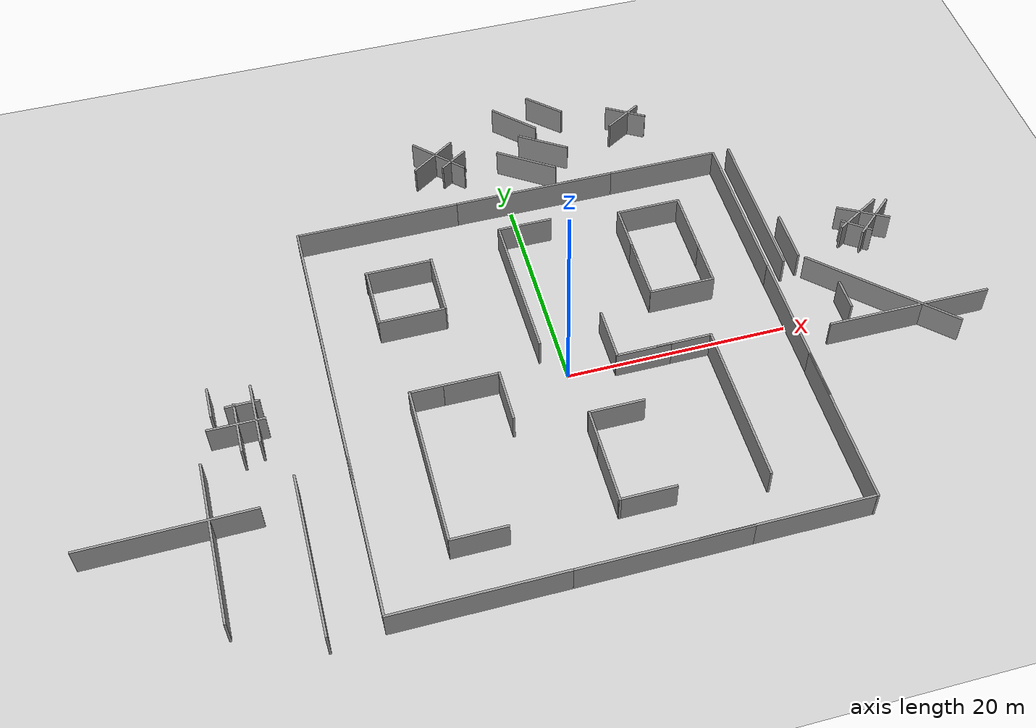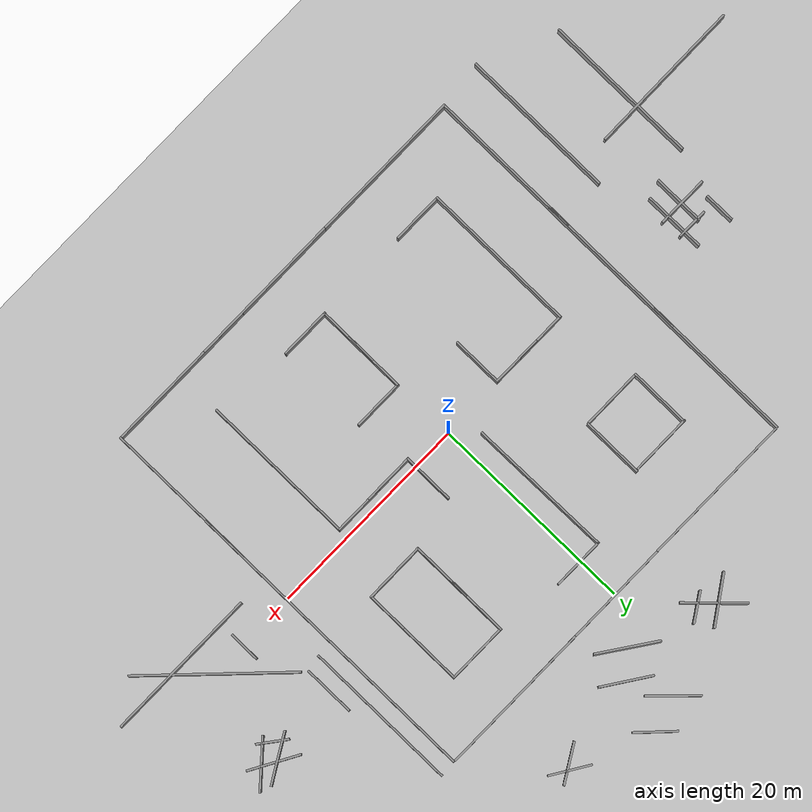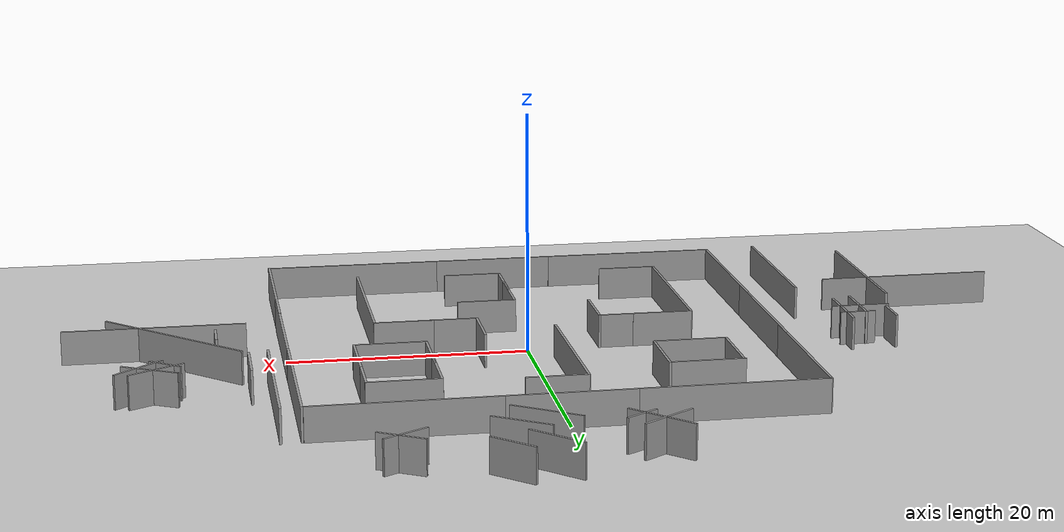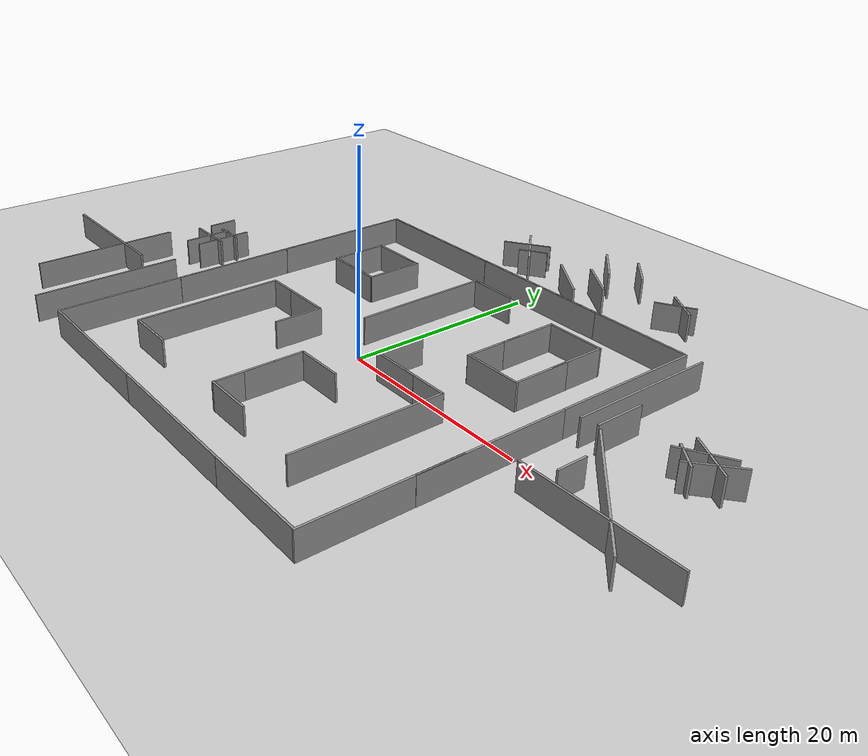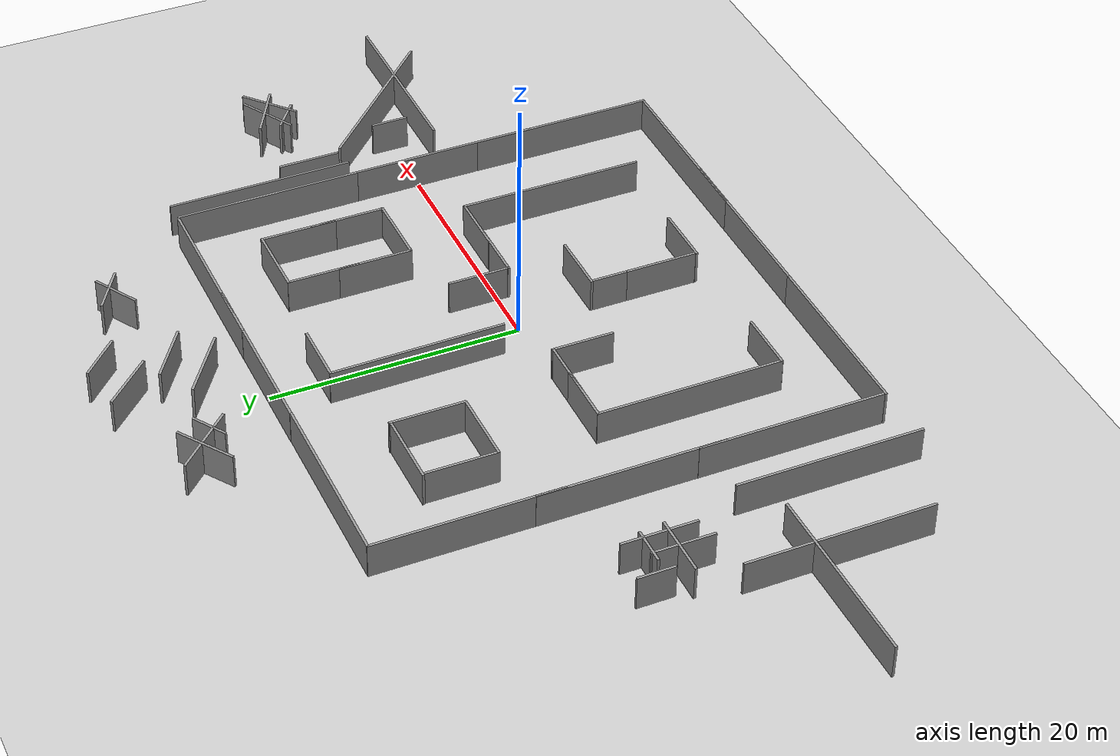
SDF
<sdf version="1.7">
 <world name="default">
  <light name="sun" type="directional">
   <pose>0 0 10 0 -0 0</pose>
   <diffuse>0.8 0.8 0.8 1</diffuse>
   <specular>0.2 0.2 0.2 1</specular>
   <attenuation>
    <range>1000</range>
    <constant>0.9</constant>
    <linear>0.01</linear>
    <quadratic>0.001</quadratic>
   </attenuation>
   <direction>-0.5 0.1 -0.9</direction>
   <spot><inner_angle>0</inner_angle><outer_angle>0</outer_angle><falloff>0</falloff></spot>
  </light>
  <model name="ground_plane">
   <static>1</static>
   <link name="link">
    <collision name="collision">
     <geometry><plane><normal>0 0 1</normal><size>100 100</size></plane></geometry>
     <surface>
      <contact><collide_bitmask>65535</collide_bitmask></contact>
      <friction><ode><mu>100</mu><mu2>50</mu2></ode></friction>
     </surface>
    </collision>
    <visual name="visual">
     <cast_shadows>0</cast_shadows>
     <geometry><plane><normal>0 0 1</normal><size>100 100</size></plane></geometry>
     <material>
      <script><uri>file://media/materials/scripts/gazebo.material</uri><name>Gazebo/Grey</name></script>
     </material>
    </visual>
   </link>
  </model>
  <gravity>0 0 -9.8</gravity>
  <magnetic_field>6e-06 2.3e-05 -4.2e-05</magnetic_field>
  <atmosphere type="adiabatic"/>
  <physics type="ode">
   <max_step_size>0.001</max_step_size>
   <real_time_factor>1</real_time_factor>
   <real_time_update_rate>1000</real_time_update_rate>
  </physics>
  <scene><ambient>0.4 0.4 0.4 1</ambient><background>0.7 0.7 0.7 1</background><shadows>1</shadows></scene>
  <spherical_coordinates>
   <surface_model>EARTH_WGS84</surface_model>
   <latitude_deg>0</latitude_deg>
   <longitude_deg>0</longitude_deg>
   <elevation>0</elevation>
   <heading_deg>0</heading_deg>
  </spherical_coordinates>
  <model name="grey_wall_3">
   <link name="link">
    <pose>0 0 1.4 0 -0 0</pose>
    <inertial>
     <mass>1</mass>
     <inertia><ixx>1</ixx><ixy>0</ixy><ixz>0</ixz><iyy>1</iyy><iyz>0</iyz><izz>1</izz></inertia>
    </inertial>
    <visual name="visual">
     <cast_shadows>0</cast_shadows>
     <geometry><box><size>3 0.2 2.8</size></box></geometry>
     <material>
      <script>
       <uri>model://grey_wall/materials/scripts</uri>
       <uri>model://grey_wall/materials/textures</uri>
       <name>vrc/grey_wall</name>
      </script>
      <shader type="pixel"><normal_map>__default__</normal_map></shader>
      <ambient>1 1 1 1</ambient>
      <diffuse>1 1 1 1</diffuse>
      <specular>0 0 0 1</specular>
      <emissive>0 0 0 1</emissive>
     </material>
    </visual>
    <collision name="collision">
     <geometry><box><size>2.96 0.2 2.8</size></box></geometry>
     <surface>
      <friction>
       <ode><mu>1</mu><mu2>1</mu2><fdir1>0 0 0</fdir1><slip1>0</slip1><slip2>0</slip2></ode>
       <torsional>
        <coefficient>1</coefficient>
        <patch_radius>0</patch_radius>
        <surface_radius>0</surface_radius>
        <use_patch_radius>1</use_patch_radius>
        <ode><slip>0</slip></ode>
       </torsional>
      </friction>
      <bounce><restitution_coefficient>0</restitution_coefficient><threshold>1e+06</threshold></bounce>
      <contact>
       <collide_without_contact>0</collide_without_contact>
       <collide_without_contact_bitmask>1</collide_without_contact_bitmask>
       <collide_bitmask>1</collide_bitmask>
       <ode>
        <soft_cfm>0</soft_cfm>
        <soft_erp>0.2</soft_erp>
        <kp>1e+13</kp>
        <kd>1</kd>
        <max_vel>0.01</max_vel>
        <min_depth>0</min_depth>
       </ode>
       <bullet>
        <split_impulse>1</split_impulse>
        <split_impulse_penetration_threshold>-0.01</split_impulse_penetration_threshold>
        <soft_cfm>0</soft_cfm>
        <soft_erp>0.2</soft_erp>
        <kp>1e+13</kp>
        <kd>1</kd>
       </bullet>
      </contact>
     </surface>
    </collision>
   </link>
   <static>1</static>
   <pose>25.6212 0.257411 0 0 0 -1.57333</pose>
  </model>
  <model name="grey_wall_3_clone">
   <link name="link">
    <pose>0 0 1.4 0 -0 0</pose>
    <inertial>
     <mass>1</mass>
     <inertia><ixx>1</ixx><ixy>0</ixy><ixz>0</ixz><iyy>1</iyy><iyz>0</iyz><izz>1</izz></inertia>
    </inertial>
    <visual name="visual">
     <cast_shadows>0</cast_shadows>
     <geometry><box><size>3 0.2 2.8</size></box></geometry>
     <material>
      <script>
       <uri>model://grey_wall/materials/scripts</uri>
       <uri>model://grey_wall/materials/textures</uri>
       <name>vrc/grey_wall</name>
      </script>
      <shader type="pixel"><normal_map>__default__</normal_map></shader>
      <ambient>1 1 1 1</ambient>
      <diffuse>1 1 1 1</diffuse>
      <specular>0 0 0 1</specular>
      <emissive>0 0 0 1</emissive>
     </material>
    </visual>
    <collision name="collision">
     <geometry><box><size>2.96 0.2 2.8</size></box></geometry>
     <surface>
      <friction>
       <ode><mu>1</mu><mu2>1</mu2><fdir1>0 0 0</fdir1><slip1>0</slip1><slip2>0</slip2></ode>
       <torsional>
        <coefficient>1</coefficient>
        <patch_radius>0</patch_radius>
        <surface_radius>0</surface_radius>
        <use_patch_radius>1</use_patch_radius>
        <ode><slip>0</slip></ode>
       </torsional>
      </friction>
      <bounce><restitution_coefficient>0</restitution_coefficient><threshold>1e+06</threshold></bounce>
      <contact>
       <collide_without_contact>0</collide_without_contact>
       <collide_without_contact_bitmask>1</collide_without_contact_bitmask>
       <collide_bitmask>1</collide_bitmask>
       <ode>
        <soft_cfm>0</soft_cfm>
        <soft_erp>0.2</soft_erp>
        <kp>1e+13</kp>
        <kd>1</kd>
        <max_vel>0.01</max_vel>
        <min_depth>0</min_depth>
       </ode>
       <bullet>
        <split_impulse>1</split_impulse>
        <split_impulse_penetration_threshold>-0.01</split_impulse_penetration_threshold>
        <soft_cfm>0</soft_cfm>
        <soft_erp>0.2</soft_erp>
        <kp>1e+13</kp>
        <kd>1</kd>
       </bullet>
      </contact>
     </surface>
    </collision>
   </link>
   <static>1</static>
   <pose>-27.6676 2.53562 0 0 -0 0</pose>
  </model>
  <model name="grey_wall_5">
   <link name="link">
    <pose>0 0 1.4 0 -0 0</pose>
    <inertial>
     <mass>1</mass>
     <inertia><ixx>1</ixx><ixy>0</ixy><ixz>0</ixz><iyy>1</iyy><iyz>0</iyz><izz>1</izz></inertia>
    </inertial>
    <visual name="visual">
     <cast_shadows>0</cast_shadows>
     <geometry><box><size>5 0.2 2.8</size></box></geometry>
     <material>
      <script>
       <uri>model://grey_wall/materials/scripts</uri>
       <uri>model://grey_wall/materials/textures</uri>
       <name>vrc/grey_wall</name>
      </script>
      <shader type="pixel"><normal_map>__default__</normal_map></shader>
      <ambient>1 1 1 1</ambient>
      <diffuse>1 1 1 1</diffuse>
      <specular>0 0 0 1</specular>
      <emissive>0 0 0 1</emissive>
     </material>
    </visual>
    <collision name="collision">
     <geometry><box><size>5 0.2 2.8</size></box></geometry>
     <surface>
      <friction>
       <ode><mu>1</mu><mu2>1</mu2><fdir1>0 0 0</fdir1><slip1>0</slip1><slip2>0</slip2></ode>
       <torsional>
        <coefficient>1</coefficient>
        <patch_radius>0</patch_radius>
        <surface_radius>0</surface_radius>
        <use_patch_radius>1</use_patch_radius>
        <ode><slip>0</slip></ode>
       </torsional>
      </friction>
      <bounce><restitution_coefficient>0</restitution_coefficient><threshold>1e+06</threshold></bounce>
      <contact>
       <collide_without_contact>0</collide_without_contact>
       <collide_without_contact_bitmask>1</collide_without_contact_bitmask>
       <collide_bitmask>1</collide_bitmask>
       <ode>
        <soft_cfm>0</soft_cfm>
        <soft_erp>0.2</soft_erp>
        <kp>1e+13</kp>
        <kd>1</kd>
        <max_vel>0.01</max_vel>
        <min_depth>0</min_depth>
       </ode>
       <bullet>
        <split_impulse>1</split_impulse>
        <split_impulse_penetration_threshold>-0.01</split_impulse_penetration_threshold>
        <soft_cfm>0</soft_cfm>
        <soft_erp>0.2</soft_erp>
        <kp>1e+13</kp>
        <kd>1</kd>
       </bullet>
      </contact>
     </surface>
    </collision>
   </link>
   <static>1</static>
   <pose>-28.4609 0.59119 0 0 0 -0.000612</pose>
  </model>
  <model name="grey_wall_15_clone_0_clone">
   <link name="link">
    <pose>0 0 1.4 0 -0 0</pose>
    <inertial>
     <mass>1</mass>
     <inertia><ixx>1</ixx><ixy>0</ixy><ixz>0</ixz><iyy>1</iyy><iyz>0</iyz><izz>1</izz></inertia>
    </inertial>
    <visual name="visual">
     <cast_shadows>0</cast_shadows>
     <geometry><box><size>15 0.2 2.8</size></box></geometry>
     <material>
      <script>
       <uri>model://grey_wall/materials/scripts</uri>
       <uri>model://grey_wall/materials/textures</uri>
       <name>vrc/grey_wall</name>
      </script>
      <shader type="pixel"><normal_map>__default__</normal_map></shader>
      <ambient>1 1 1 1</ambient>
      <diffuse>1 1 1 1</diffuse>
      <specular>0 0 0 1</specular>
      <emissive>0 0 0 1</emissive>
     </material>
    </visual>
    <collision name="collision">
     <geometry><box><size>15 0.2 2.8</size></box></geometry>
     <surface>
      <friction>
       <ode><mu>1</mu><mu2>1</mu2><fdir1>0 0 0</fdir1><slip1>0</slip1><slip2>0</slip2></ode>
       <torsional>
        <coefficient>1</coefficient>
        <patch_radius>0</patch_radius>
        <surface_radius>0</surface_radius>
        <use_patch_radius>1</use_patch_radius>
        <ode><slip>0</slip></ode>
       </torsional>
      </friction>
      <bounce><restitution_coefficient>0</restitution_coefficient><threshold>1e+06</threshold></bounce>
      <contact>
       <collide_without_contact>0</collide_without_contact>
       <collide_without_contact_bitmask>1</collide_without_contact_bitmask>
       <collide_bitmask>1</collide_bitmask>
       <ode>
        <soft_cfm>0</soft_cfm>
        <soft_erp>0.2</soft_erp>
        <kp>1e+13</kp>
        <kd>1</kd>
        <max_vel>0.01</max_vel>
        <min_depth>0</min_depth>
       </ode>
       <bullet>
        <split_impulse>1</split_impulse>
        <split_impulse_penetration_threshold>-0.01</split_impulse_penetration_threshold>
        <soft_cfm>0</soft_cfm>
        <soft_erp>0.2</soft_erp>
        <kp>1e+13</kp>
        <kd>1</kd>
       </bullet>
      </contact>
     </surface>
    </collision>
   </link>
   <static>1</static>
   <pose>-31.7874 -10.0693 0 0 -0 1.57141</pose>
  </model>
  <model name="grey_wall_5_clone_0">
   <link name="link">
    <pose>0 0 1.4 0 -0 0</pose>
    <inertial>
     <mass>1</mass>
     <inertia><ixx>1</ixx><ixy>0</ixy><ixz>0</ixz><iyy>1</iyy><iyz>0</iyz><izz>1</izz></inertia>
    </inertial>
    <visual name="visual">
     <cast_shadows>0</cast_shadows>
     <geometry><box><size>5 0.2 2.8</size></box></geometry>
     <material>
      <script>
       <uri>model://grey_wall/materials/scripts</uri>
       <uri>model://grey_wall/materials/textures</uri>
       <name>vrc/grey_wall</name>
      </script>
      <shader type="pixel"><normal_map>__default__</normal_map></shader>
      <ambient>1 1 1 1</ambient>
      <diffuse>1 1 1 1</diffuse>
      <specular>0 0 0 1</specular>
      <emissive>0 0 0 1</emissive>
     </material>
    </visual>
    <collision name="collision">
     <geometry><box><size>5 0.2 2.8</size></box></geometry>
     <surface>
      <friction>
       <ode><mu>1</mu><mu2>1</mu2><fdir1>0 0 0</fdir1><slip1>0</slip1><slip2>0</slip2></ode>
       <torsional>
        <coefficient>1</coefficient>
        <patch_radius>0</patch_radius>
        <surface_radius>0</surface_radius>
        <use_patch_radius>1</use_patch_radius>
        <ode><slip>0</slip></ode>
       </torsional>
      </friction>
      <bounce><restitution_coefficient>0</restitution_coefficient><threshold>1e+06</threshold></bounce>
      <contact>
       <collide_without_contact>0</collide_without_contact>
       <collide_without_contact_bitmask>1</collide_without_contact_bitmask>
       <collide_bitmask>1</collide_bitmask>
       <ode>
        <soft_cfm>0</soft_cfm>
        <soft_erp>0.2</soft_erp>
        <kp>1e+13</kp>
        <kd>1</kd>
        <max_vel>0.01</max_vel>
        <min_depth>0</min_depth>
       </ode>
       <bullet>
        <split_impulse>1</split_impulse>
        <split_impulse_penetration_threshold>-0.01</split_impulse_penetration_threshold>
        <soft_cfm>0</soft_cfm>
        <soft_erp>0.2</soft_erp>
        <kp>1e+13</kp>
        <kd>1</kd>
       </bullet>
      </contact>
     </surface>
    </collision>
   </link>
   <static>1</static>
   <pose>30.4979 9.05013 0 0 -0 0.529284</pose>
  </model>
  <model name="grey_wall_5_clone_1">
   <link name="link">
    <pose>0 0 1.4 0 -0 0</pose>
    <inertial>
     <mass>1</mass>
     <inertia><ixx>1</ixx><ixy>0</ixy><ixz>0</ixz><iyy>1</iyy><iyz>0</iyz><izz>1</izz></inertia>
    </inertial>
    <visual name="visual">
     <cast_shadows>0</cast_shadows>
     <geometry><box><size>5 0.2 2.8</size></box></geometry>
     <material>
      <script>
       <uri>model://grey_wall/materials/scripts</uri>
       <uri>model://grey_wall/materials/textures</uri>
       <name>vrc/grey_wall</name>
      </script>
      <shader type="pixel"><normal_map>__default__</normal_map></shader>
      <ambient>1 1 1 1</ambient>
      <diffuse>1 1 1 1</diffuse>
      <specular>0 0 0 1</specular>
      <emissive>0 0 0 1</emissive>
     </material>
    </visual>
    <collision name="collision">
     <geometry><box><size>5 0.2 2.8</size></box></geometry>
     <surface>
      <friction>
       <ode><mu>1</mu><mu2>1</mu2><fdir1>0 0 0</fdir1><slip1>0</slip1><slip2>0</slip2></ode>
       <torsional>
        <coefficient>1</coefficient>
        <patch_radius>0</patch_radius>
        <surface_radius>0</surface_radius>
        <use_patch_radius>1</use_patch_radius>
        <ode><slip>0</slip></ode>
       </torsional>
      </friction>
      <bounce><restitution_coefficient>0</restitution_coefficient><threshold>1e+06</threshold></bounce>
      <contact>
       <collide_without_contact>0</collide_without_contact>
       <collide_without_contact_bitmask>1</collide_without_contact_bitmask>
       <collide_bitmask>1</collide_bitmask>
       <ode>
        <soft_cfm>0</soft_cfm>
        <soft_erp>0.2</soft_erp>
        <kp>1e+13</kp>
        <kd>1</kd>
        <max_vel>0.01</max_vel>
        <min_depth>0</min_depth>
       </ode>
       <bullet>
        <split_impulse>1</split_impulse>
        <split_impulse_penetration_threshold>-0.01</split_impulse_penetration_threshold>
        <soft_cfm>0</soft_cfm>
        <soft_erp>0.2</soft_erp>
        <kp>1e+13</kp>
        <kd>1</kd>
       </bullet>
      </contact>
     </surface>
    </collision>
   </link>
   <static>1</static>
   <pose>31.0104 9.05146 0 0 0 -0.50895</pose>
  </model>
  <model name="grey_wall_5_clone_clone_0_clone_0">
   <link name="link">
    <pose>0 0 1.4 0 -0 0</pose>
    <inertial>
     <mass>1</mass>
     <inertia><ixx>1</ixx><ixy>0</ixy><ixz>0</ixz><iyy>1</iyy><iyz>0</iyz><izz>1</izz></inertia>
    </inertial>
    <visual name="visual">
     <cast_shadows>0</cast_shadows>
     <geometry><box><size>5 0.2 2.8</size></box></geometry>
     <material>
      <script>
       <uri>model://grey_wall/materials/scripts</uri>
       <uri>model://grey_wall/materials/textures</uri>
       <name>vrc/grey_wall</name>
      </script>
      <shader type="pixel"><normal_map>__default__</normal_map></shader>
      <ambient>1 1 1 1</ambient>
      <diffuse>1 1 1 1</diffuse>
      <specular>0 0 0 1</specular>
      <emissive>0 0 0 1</emissive>
     </material>
    </visual>
    <collision name="collision">
     <geometry><box><size>5 0.2 2.8</size></box></geometry>
     <surface>
      <friction>
       <ode><mu>1</mu><mu2>1</mu2><fdir1>0 0 0</fdir1><slip1>0</slip1><slip2>0</slip2></ode>
       <torsional>
        <coefficient>1</coefficient>
        <patch_radius>0</patch_radius>
        <surface_radius>0</surface_radius>
        <use_patch_radius>1</use_patch_radius>
        <ode><slip>0</slip></ode>
       </torsional>
      </friction>
      <bounce><restitution_coefficient>0</restitution_coefficient><threshold>1e+06</threshold></bounce>
      <contact>
       <collide_without_contact>0</collide_without_contact>
       <collide_without_contact_bitmask>1</collide_without_contact_bitmask>
       <collide_bitmask>1</collide_bitmask>
       <ode>
        <soft_cfm>0</soft_cfm>
        <soft_erp>0.2</soft_erp>
        <kp>1e+13</kp>
        <kd>1</kd>
        <max_vel>0.01</max_vel>
        <min_depth>0</min_depth>
       </ode>
       <bullet>
        <split_impulse>1</split_impulse>
        <split_impulse_penetration_threshold>-0.01</split_impulse_penetration_threshold>
        <soft_cfm>0</soft_cfm>
        <soft_erp>0.2</soft_erp>
        <kp>1e+13</kp>
        <kd>1</kd>
       </bullet>
      </contact>
     </surface>
    </collision>
   </link>
   <static>1</static>
   <pose>-28.3665 0.251575 0 0 -0 1.57141</pose>
  </model>
  <model name="grey_wall_5_clone_clone_0_clone_1_clone">
   <link name="link">
    <pose>0 0 1.4 0 -0 0</pose>
    <inertial>
     <mass>1</mass>
     <inertia><ixx>1</ixx><ixy>0</ixy><ixz>0</ixz><iyy>1</iyy><iyz>0</iyz><izz>1</izz></inertia>
    </inertial>
    <visual name="visual">
     <cast_shadows>0</cast_shadows>
     <geometry><box><size>5 0.2 2.8</size></box></geometry>
     <material>
      <script>
       <uri>model://grey_wall/materials/scripts</uri>
       <uri>model://grey_wall/materials/textures</uri>
       <name>vrc/grey_wall</name>
      </script>
      <shader type="pixel"><normal_map>__default__</normal_map></shader>
      <ambient>1 1 1 1</ambient>
      <diffuse>1 1 1 1</diffuse>
      <specular>0 0 0 1</specular>
      <emissive>0 0 0 1</emissive>
     </material>
    </visual>
    <collision name="collision">
     <geometry><box><size>5 0.2 2.8</size></box></geometry>
     <surface>
      <friction>
       <ode><mu>1</mu><mu2>1</mu2><fdir1>0 0 0</fdir1><slip1>0</slip1><slip2>0</slip2></ode>
       <torsional>
        <coefficient>1</coefficient>
        <patch_radius>0</patch_radius>
        <surface_radius>0</surface_radius>
        <use_patch_radius>1</use_patch_radius>
        <ode><slip>0</slip></ode>
       </torsional>
      </friction>
      <bounce><restitution_coefficient>0</restitution_coefficient><threshold>1e+06</threshold></bounce>
      <contact>
       <collide_without_contact>0</collide_without_contact>
       <collide_without_contact_bitmask>1</collide_without_contact_bitmask>
       <collide_bitmask>1</collide_bitmask>
       <ode>
        <soft_cfm>0</soft_cfm>
        <soft_erp>0.2</soft_erp>
        <kp>1e+13</kp>
        <kd>1</kd>
        <max_vel>0.01</max_vel>
        <min_depth>0</min_depth>
       </ode>
       <bullet>
        <split_impulse>1</split_impulse>
        <split_impulse_penetration_threshold>-0.01</split_impulse_penetration_threshold>
        <soft_cfm>0</soft_cfm>
        <soft_erp>0.2</soft_erp>
        <kp>1e+13</kp>
        <kd>1</kd>
       </bullet>
      </contact>
     </surface>
    </collision>
   </link>
   <static>1</static>
   <pose>-5.91123 26.8606 0 0 -0 0.603575</pose>
  </model>
  <model name="grey_wall_5_clone_clone_0_clone_1_clone_0">
   <link name="link">
    <pose>0 0 1.4 0 -0 0</pose>
    <inertial>
     <mass>1</mass>
     <inertia><ixx>1</ixx><ixy>0</ixy><ixz>0</ixz><iyy>1</iyy><iyz>0</iyz><izz>1</izz></inertia>
    </inertial>
    <visual name="visual">
     <cast_shadows>0</cast_shadows>
     <geometry><box><size>5 0.2 2.8</size></box></geometry>
     <material>
      <script>
       <uri>model://grey_wall/materials/scripts</uri>
       <uri>model://grey_wall/materials/textures</uri>
       <name>vrc/grey_wall</name>
      </script>
      <shader type="pixel"><normal_map>__default__</normal_map></shader>
      <ambient>1 1 1 1</ambient>
      <diffuse>1 1 1 1</diffuse>
      <specular>0 0 0 1</specular>
      <emissive>0 0 0 1</emissive>
     </material>
    </visual>
    <collision name="collision">
     <geometry><box><size>5 0.2 2.8</size></box></geometry>
     <surface>
      <friction>
       <ode><mu>1</mu><mu2>1</mu2><fdir1>0 0 0</fdir1><slip1>0</slip1><slip2>0</slip2></ode>
       <torsional>
        <coefficient>1</coefficient>
        <patch_radius>0</patch_radius>
        <surface_radius>0</surface_radius>
        <use_patch_radius>1</use_patch_radius>
        <ode><slip>0</slip></ode>
       </torsional>
      </friction>
      <bounce><restitution_coefficient>0</restitution_coefficient><threshold>1e+06</threshold></bounce>
      <contact>
       <collide_without_contact>0</collide_without_contact>
       <collide_without_contact_bitmask>1</collide_without_contact_bitmask>
       <collide_bitmask>1</collide_bitmask>
       <ode>
        <soft_cfm>0</soft_cfm>
        <soft_erp>0.2</soft_erp>
        <kp>1e+13</kp>
        <kd>1</kd>
        <max_vel>0.01</max_vel>
        <min_depth>0</min_depth>
       </ode>
       <bullet>
        <split_impulse>1</split_impulse>
        <split_impulse_penetration_threshold>-0.01</split_impulse_penetration_threshold>
        <soft_cfm>0</soft_cfm>
        <soft_erp>0.2</soft_erp>
        <kp>1e+13</kp>
        <kd>1</kd>
       </bullet>
      </contact>
     </surface>
    </collision>
   </link>
   <static>1</static>
   <pose>4.749 26.0113 0 0 -0 2.55063</pose>
  </model>
  <model name="grey_wall_4_clone_0_clone_clone_0_clone_clone_clone_1_clone">
   <link name="link">
    <pose>0 0 1.4 0 -0 0</pose>
    <inertial>
     <mass>1</mass>
     <inertia><ixx>1</ixx><ixy>0</ixy><ixz>0</ixz><iyy>1</iyy><iyz>0</iyz><izz>1</izz></inertia>
    </inertial>
    <visual name="visual">
     <cast_shadows>0</cast_shadows>
     <geometry><box><size>4 0.2 2.8</size></box></geometry>
     <material>
      <script>
       <uri>model://grey_wall/materials/scripts</uri>
       <uri>model://grey_wall/materials/textures</uri>
       <name>vrc/grey_wall</name>
      </script>
      <shader type="pixel"><normal_map>__default__</normal_map></shader>
      <ambient>1 1 1 1</ambient>
      <diffuse>1 1 1 1</diffuse>
      <specular>0 0 0 1</specular>
      <emissive>0 0 0 1</emissive>
     </material>
    </visual>
    <collision name="collision">
     <geometry><box><size>4 0.2 2.8</size></box></geometry>
     <surface>
      <friction>
       <ode><mu>1</mu><mu2>1</mu2><fdir1>0 0 0</fdir1><slip1>0</slip1><slip2>0</slip2></ode>
       <torsional>
        <coefficient>1</coefficient>
        <patch_radius>0</patch_radius>
        <surface_radius>0</surface_radius>
        <use_patch_radius>1</use_patch_radius>
        <ode><slip>0</slip></ode>
       </torsional>
      </friction>
      <bounce><restitution_coefficient>0</restitution_coefficient><threshold>1e+06</threshold></bounce>
      <contact>
       <collide_without_contact>0</collide_without_contact>
       <collide_without_contact_bitmask>1</collide_without_contact_bitmask>
       <collide_bitmask>1</collide_bitmask>
       <ode>
        <soft_cfm>0</soft_cfm>
        <soft_erp>0.2</soft_erp>
        <kp>1e+13</kp>
        <kd>1</kd>
        <max_vel>0.01</max_vel>
        <min_depth>0</min_depth>
       </ode>
       <bullet>
        <split_impulse>1</split_impulse>
        <split_impulse_penetration_threshold>-0.01</split_impulse_penetration_threshold>
        <soft_cfm>0</soft_cfm>
        <soft_erp>0.2</soft_erp>
        <kp>1e+13</kp>
        <kd>1</kd>
       </bullet>
      </contact>
     </surface>
    </collision>
   </link>
   <static>1</static>
   <pose>13.6601 27.8625 0 0 -0 2.58708</pose>
  </model>
  <model name="grey_wall_5_clone_clone_0_clone_1_clone_clone_0">
   <link name="link">
    <pose>0 0 1.4 0 -0 0</pose>
    <inertial>
     <mass>1</mass>
     <inertia><ixx>1</ixx><ixy>0</ixy><ixz>0</ixz><iyy>1</iyy><iyz>0</iyz><izz>1</izz></inertia>
    </inertial>
    <visual name="visual">
     <cast_shadows>0</cast_shadows>
     <geometry><box><size>5 0.2 2.8</size></box></geometry>
     <material>
      <script>
       <uri>model://grey_wall/materials/scripts</uri>
       <uri>model://grey_wall/materials/textures</uri>
       <name>vrc/grey_wall</name>
      </script>
      <shader type="pixel"><normal_map>__default__</normal_map></shader>
      <ambient>1 1 1 1</ambient>
      <diffuse>1 1 1 1</diffuse>
      <specular>0 0 0 1</specular>
      <emissive>0 0 0 1</emissive>
     </material>
    </visual>
    <collision name="collision">
     <geometry><box><size>5 0.2 2.8</size></box></geometry>
     <surface>
      <friction>
       <ode><mu>1</mu><mu2>1</mu2><fdir1>0 0 0</fdir1><slip1>0</slip1><slip2>0</slip2></ode>
       <torsional>
        <coefficient>1</coefficient>
        <patch_radius>0</patch_radius>
        <surface_radius>0</surface_radius>
        <use_patch_radius>1</use_patch_radius>
        <ode><slip>0</slip></ode>
       </torsional>
      </friction>
      <bounce><restitution_coefficient>0</restitution_coefficient><threshold>1e+06</threshold></bounce>
      <contact>
       <collide_without_contact>0</collide_without_contact>
       <collide_without_contact_bitmask>1</collide_without_contact_bitmask>
       <collide_bitmask>1</collide_bitmask>
       <ode>
        <soft_cfm>0</soft_cfm>
        <soft_erp>0.2</soft_erp>
        <kp>1e+13</kp>
        <kd>1</kd>
        <max_vel>0.01</max_vel>
        <min_depth>0</min_depth>
       </ode>
       <bullet>
        <split_impulse>1</split_impulse>
        <split_impulse_penetration_threshold>-0.01</split_impulse_penetration_threshold>
        <soft_cfm>0</soft_cfm>
        <soft_erp>0.2</soft_erp>
        <kp>1e+13</kp>
        <kd>1</kd>
       </bullet>
      </contact>
     </surface>
    </collision>
   </link>
   <static>1</static>
   <pose>31.859 8.37092 0 0 -0 0.722717</pose>
  </model>
  <model name="grey_wall_6">
   <link name="link">
    <pose>0 0 1.4 0 -0 0</pose>
    <inertial>
     <mass>1</mass>
     <inertia><ixx>1</ixx><ixy>0</ixy><ixz>0</ixz><iyy>1</iyy><iyz>0</iyz><izz>1</izz></inertia>
    </inertial>
    <visual name="visual">
     <cast_shadows>0</cast_shadows>
     <geometry><box><size>6 0.2 2.8</size></box></geometry>
     <material>
      <script>
       <uri>model://grey_wall/materials/scripts</uri>
       <uri>model://grey_wall/materials/textures</uri>
       <name>vrc/grey_wall</name>
      </script>
      <shader type="pixel"><normal_map>__default__</normal_map></shader>
      <ambient>1 1 1 1</ambient>
      <diffuse>1 1 1 1</diffuse>
      <specular>0 0 0 1</specular>
      <emissive>0 0 0 1</emissive>
     </material>
    </visual>
    <collision name="collision">
     <geometry><box><size>6 0.2 2.8</size></box></geometry>
     <surface>
      <friction>
       <ode><mu>1</mu><mu2>1</mu2><fdir1>0 0 0</fdir1><slip1>0</slip1><slip2>0</slip2></ode>
       <torsional>
        <coefficient>1</coefficient>
        <patch_radius>0</patch_radius>
        <surface_radius>0</surface_radius>
        <use_patch_radius>1</use_patch_radius>
        <ode><slip>0</slip></ode>
       </torsional>
      </friction>
      <bounce><restitution_coefficient>0</restitution_coefficient><threshold>1e+06</threshold></bounce>
      <contact>
       <collide_without_contact>0</collide_without_contact>
       <collide_without_contact_bitmask>1</collide_without_contact_bitmask>
       <collide_bitmask>1</collide_bitmask>
       <ode>
        <soft_cfm>0</soft_cfm>
        <soft_erp>0.2</soft_erp>
        <kp>1e+13</kp>
        <kd>1</kd>
        <max_vel>0.01</max_vel>
        <min_depth>0</min_depth>
       </ode>
       <bullet>
        <split_impulse>1</split_impulse>
        <split_impulse_penetration_threshold>-0.01</split_impulse_penetration_threshold>
        <soft_cfm>0</soft_cfm>
        <soft_erp>0.2</soft_erp>
        <kp>1e+13</kp>
        <kd>1</kd>
       </bullet>
      </contact>
     </surface>
    </collision>
   </link>
   <static>1</static>
   <pose>-5.41021 26.7468 0 0 -0 2.33668</pose>
  </model>
  <model name="grey_wall_6_clone">
   <link name="link">
    <pose>0 0 1.4 0 -0 0</pose>
    <inertial>
     <mass>1</mass>
     <inertia><ixx>1</ixx><ixy>0</ixy><ixz>0</ixz><iyy>1</iyy><iyz>0</iyz><izz>1</izz></inertia>
    </inertial>
    <visual name="visual">
     <cast_shadows>0</cast_shadows>
     <geometry><box><size>6 0.2 2.8</size></box></geometry>
     <material>
      <script>
       <uri>model://grey_wall/materials/scripts</uri>
       <uri>model://grey_wall/materials/textures</uri>
       <name>vrc/grey_wall</name>
      </script>
      <shader type="pixel"><normal_map>__default__</normal_map></shader>
      <ambient>1 1 1 1</ambient>
      <diffuse>1 1 1 1</diffuse>
      <specular>0 0 0 1</specular>
      <emissive>0 0 0 1</emissive>
     </material>
    </visual>
    <collision name="collision">
     <geometry><box><size>6 0.2 2.8</size></box></geometry>
     <surface>
      <friction>
       <ode><mu>1</mu><mu2>1</mu2><fdir1>0 0 0</fdir1><slip1>0</slip1><slip2>0</slip2></ode>
       <torsional>
        <coefficient>1</coefficient>
        <patch_radius>0</patch_radius>
        <surface_radius>0</surface_radius>
        <use_patch_radius>1</use_patch_radius>
        <ode><slip>0</slip></ode>
       </torsional>
      </friction>
      <bounce><restitution_coefficient>0</restitution_coefficient><threshold>1e+06</threshold></bounce>
      <contact>
       <collide_without_contact>0</collide_without_contact>
       <collide_without_contact_bitmask>1</collide_without_contact_bitmask>
       <collide_bitmask>1</collide_bitmask>
       <ode>
        <soft_cfm>0</soft_cfm>
        <soft_erp>0.2</soft_erp>
        <kp>1e+13</kp>
        <kd>1</kd>
        <max_vel>0.01</max_vel>
        <min_depth>0</min_depth>
       </ode>
       <bullet>
        <split_impulse>1</split_impulse>
        <split_impulse_penetration_threshold>-0.01</split_impulse_penetration_threshold>
        <soft_cfm>0</soft_cfm>
        <soft_erp>0.2</soft_erp>
        <kp>1e+13</kp>
        <kd>1</kd>
       </bullet>
      </contact>
     </surface>
    </collision>
   </link>
   <static>1</static>
   <pose>-26.7573 1.28858 0 0 -0 1.57141</pose>
  </model>
  <model name="grey_wall_5_clone_clone_0_clone_1_clone_0_clone_0">
   <link name="link">
    <pose>0 0 1.4 0 -0 0</pose>
    <inertial>
     <mass>1</mass>
     <inertia><ixx>1</ixx><ixy>0</ixy><ixz>0</ixz><iyy>1</iyy><iyz>0</iyz><izz>1</izz></inertia>
    </inertial>
    <visual name="visual">
     <cast_shadows>0</cast_shadows>
     <geometry><box><size>5 0.2 2.8</size></box></geometry>
     <material>
      <script>
       <uri>model://grey_wall/materials/scripts</uri>
       <uri>model://grey_wall/materials/textures</uri>
       <name>vrc/grey_wall</name>
      </script>
      <shader type="pixel"><normal_map>__default__</normal_map></shader>
      <ambient>1 1 1 1</ambient>
      <diffuse>1 1 1 1</diffuse>
      <specular>0 0 0 1</specular>
      <emissive>0 0 0 1</emissive>
     </material>
    </visual>
    <collision name="collision">
     <geometry><box><size>5 0.2 2.8</size></box></geometry>
     <surface>
      <friction>
       <ode><mu>1</mu><mu2>1</mu2><fdir1>0 0 0</fdir1><slip1>0</slip1><slip2>0</slip2></ode>
       <torsional>
        <coefficient>1</coefficient>
        <patch_radius>0</patch_radius>
        <surface_radius>0</surface_radius>
        <use_patch_radius>1</use_patch_radius>
        <ode><slip>0</slip></ode>
       </torsional>
      </friction>
      <bounce><restitution_coefficient>0</restitution_coefficient><threshold>1e+06</threshold></bounce>
      <contact>
       <collide_without_contact>0</collide_without_contact>
       <collide_without_contact_bitmask>1</collide_without_contact_bitmask>
       <collide_bitmask>1</collide_bitmask>
       <ode>
        <soft_cfm>0</soft_cfm>
        <soft_erp>0.2</soft_erp>
        <kp>1e+13</kp>
        <kd>1</kd>
        <max_vel>0.01</max_vel>
        <min_depth>0</min_depth>
       </ode>
       <bullet>
        <split_impulse>1</split_impulse>
        <split_impulse_penetration_threshold>-0.01</split_impulse_penetration_threshold>
        <soft_cfm>0</soft_cfm>
        <soft_erp>0.2</soft_erp>
        <kp>1e+13</kp>
        <kd>1</kd>
       </bullet>
      </contact>
     </surface>
    </collision>
   </link>
   <static>1</static>
   <pose>4.10333 1.50808 0 0 -0 1.57141</pose>
  </model>
  <model name="grey_wall_6_clone_clone_1">
   <link name="link">
    <pose>0 0 1.4 0 -0 0</pose>
    <inertial>
     <mass>1</mass>
     <inertia><ixx>1</ixx><ixy>0</ixy><ixz>0</ixz><iyy>1</iyy><iyz>0</iyz><izz>1</izz></inertia>
    </inertial>
    <visual name="visual">
     <cast_shadows>0</cast_shadows>
     <geometry><box><size>6 0.2 2.8</size></box></geometry>
     <material>
      <script>
       <uri>model://grey_wall/materials/scripts</uri>
       <uri>model://grey_wall/materials/textures</uri>
       <name>vrc/grey_wall</name>
      </script>
      <shader type="pixel"><normal_map>__default__</normal_map></shader>
      <ambient>1 1 1 1</ambient>
      <diffuse>1 1 1 1</diffuse>
      <specular>0 0 0 1</specular>
      <emissive>0 0 0 1</emissive>
     </material>
    </visual>
    <collision name="collision">
     <geometry><box><size>6 0.2 2.8</size></box></geometry>
     <surface>
      <friction>
       <ode><mu>1</mu><mu2>1</mu2><fdir1>0 0 0</fdir1><slip1>0</slip1><slip2>0</slip2></ode>
       <torsional>
        <coefficient>1</coefficient>
        <patch_radius>0</patch_radius>
        <surface_radius>0</surface_radius>
        <use_patch_radius>1</use_patch_radius>
        <ode><slip>0</slip></ode>
       </torsional>
      </friction>
      <bounce><restitution_coefficient>0</restitution_coefficient><threshold>1e+06</threshold></bounce>
      <contact>
       <collide_without_contact>0</collide_without_contact>
       <collide_without_contact_bitmask>1</collide_without_contact_bitmask>
       <collide_bitmask>1</collide_bitmask>
       <ode>
        <soft_cfm>0</soft_cfm>
        <soft_erp>0.2</soft_erp>
        <kp>1e+13</kp>
        <kd>1</kd>
        <max_vel>0.01</max_vel>
        <min_depth>0</min_depth>
       </ode>
       <bullet>
        <split_impulse>1</split_impulse>
        <split_impulse_penetration_threshold>-0.01</split_impulse_penetration_threshold>
        <soft_cfm>0</soft_cfm>
        <soft_erp>0.2</soft_erp>
        <kp>1e+13</kp>
        <kd>1</kd>
       </bullet>
      </contact>
     </surface>
    </collision>
   </link>
   <static>1</static>
   <pose>2.60048 24.0847 -1e-06 -0.017688 -0 2.53788</pose>
  </model>
  <model name="grey_wall_4_clone_clone">
   <link name="link">
    <pose>0 0 1.4 0 -0 0</pose>
    <inertial>
     <mass>1</mass>
     <inertia><ixx>1</ixx><ixy>0</ixy><ixz>0</ixz><iyy>1</iyy><iyz>0</iyz><izz>1</izz></inertia>
    </inertial>
    <visual name="visual">
     <cast_shadows>0</cast_shadows>
     <geometry><box><size>4 0.2 2.8</size></box></geometry>
     <material>
      <script>
       <uri>model://grey_wall/materials/scripts</uri>
       <uri>model://grey_wall/materials/textures</uri>
       <name>vrc/grey_wall</name>
      </script>
      <shader type="pixel"><normal_map>__default__</normal_map></shader>
      <ambient>1 1 1 1</ambient>
      <diffuse>1 1 1 1</diffuse>
      <specular>0 0 0 1</specular>
      <emissive>0 0 0 1</emissive>
     </material>
    </visual>
    <collision name="collision">
     <geometry><box><size>4 0.2 2.8</size></box></geometry>
     <surface>
      <friction>
       <ode><mu>1</mu><mu2>1</mu2><fdir1>0 0 0</fdir1><slip1>0</slip1><slip2>0</slip2></ode>
       <torsional>
        <coefficient>1</coefficient>
        <patch_radius>0</patch_radius>
        <surface_radius>0</surface_radius>
        <use_patch_radius>1</use_patch_radius>
        <ode><slip>0</slip></ode>
       </torsional>
      </friction>
      <bounce><restitution_coefficient>0</restitution_coefficient><threshold>1e+06</threshold></bounce>
      <contact>
       <collide_without_contact>0</collide_without_contact>
       <collide_without_contact_bitmask>1</collide_without_contact_bitmask>
       <collide_bitmask>1</collide_bitmask>
       <ode>
        <soft_cfm>0</soft_cfm>
        <soft_erp>0.2</soft_erp>
        <kp>1e+13</kp>
        <kd>1</kd>
        <max_vel>0.01</max_vel>
        <min_depth>0</min_depth>
       </ode>
       <bullet>
        <split_impulse>1</split_impulse>
        <split_impulse_penetration_threshold>-0.01</split_impulse_penetration_threshold>
        <soft_cfm>0</soft_cfm>
        <soft_erp>0.2</soft_erp>
        <kp>1e+13</kp>
        <kd>1</kd>
       </bullet>
      </contact>
     </surface>
    </collision>
   </link>
   <static>1</static>
   <pose>13.2894 27.4013 0 0 -0 0.540349</pose>
  </model>
  <model name="grey_wall_3_clone_clone_clone">
   <link name="link">
    <pose>0 0 1.4 0 -0 0</pose>
    <inertial>
     <mass>1</mass>
     <inertia><ixx>1</ixx><ixy>0</ixy><ixz>0</ixz><iyy>1</iyy><iyz>0</iyz><izz>1</izz></inertia>
    </inertial>
    <visual name="visual">
     <cast_shadows>0</cast_shadows>
     <geometry><box><size>3 0.2 2.8</size></box></geometry>
     <material>
      <script>
       <uri>model://grey_wall/materials/scripts</uri>
       <uri>model://grey_wall/materials/textures</uri>
       <name>vrc/grey_wall</name>
      </script>
      <shader type="pixel"><normal_map>__default__</normal_map></shader>
      <ambient>1 1 1 1</ambient>
      <diffuse>1 1 1 1</diffuse>
      <specular>0 0 0 1</specular>
      <emissive>0 0 0 1</emissive>
     </material>
    </visual>
    <collision name="collision">
     <geometry><box><size>2.96 0.2 2.8</size></box></geometry>
     <surface>
      <friction>
       <ode><mu>1</mu><mu2>1</mu2><fdir1>0 0 0</fdir1><slip1>0</slip1><slip2>0</slip2></ode>
       <torsional>
        <coefficient>1</coefficient>
        <patch_radius>0</patch_radius>
        <surface_radius>0</surface_radius>
        <use_patch_radius>1</use_patch_radius>
        <ode><slip>0</slip></ode>
       </torsional>
      </friction>
      <bounce><restitution_coefficient>0</restitution_coefficient><threshold>1e+06</threshold></bounce>
      <contact>
       <collide_without_contact>0</collide_without_contact>
       <collide_without_contact_bitmask>1</collide_without_contact_bitmask>
       <collide_bitmask>1</collide_bitmask>
       <ode>
        <soft_cfm>0</soft_cfm>
        <soft_erp>0.2</soft_erp>
        <kp>1e+13</kp>
        <kd>1</kd>
        <max_vel>0.01</max_vel>
        <min_depth>0</min_depth>
       </ode>
       <bullet>
        <split_impulse>1</split_impulse>
        <split_impulse_penetration_threshold>-0.01</split_impulse_penetration_threshold>
        <soft_cfm>0</soft_cfm>
        <soft_erp>0.2</soft_erp>
        <kp>1e+13</kp>
        <kd>1</kd>
       </bullet>
      </contact>
     </surface>
    </collision>
   </link>
   <static>1</static>
   <pose>-4.12474 25.9342 0 0 -0 0.580341</pose>
  </model>
  <model name="grey_wall_15_clone_0_clone_clone">
   <link name="link">
    <pose>0 0 1.4 0 -0 0</pose>
    <inertial>
     <mass>1</mass>
     <inertia><ixx>1</ixx><ixy>0</ixy><ixz>0</ixz><iyy>1</iyy><iyz>0</iyz><izz>1</izz></inertia>
    </inertial>
    <visual name="visual">
     <cast_shadows>0</cast_shadows>
     <geometry><box><size>15 0.2 2.8</size></box></geometry>
     <material>
      <script>
       <uri>model://grey_wall/materials/scripts</uri>
       <uri>model://grey_wall/materials/textures</uri>
       <name>vrc/grey_wall</name>
      </script>
      <shader type="pixel"><normal_map>__default__</normal_map></shader>
      <ambient>1 1 1 1</ambient>
      <diffuse>1 1 1 1</diffuse>
      <specular>0 0 0 1</specular>
      <emissive>0 0 0 1</emissive>
     </material>
    </visual>
    <collision name="collision">
     <geometry><box><size>15 0.2 2.8</size></box></geometry>
     <surface>
      <friction>
       <ode><mu>1</mu><mu2>1</mu2><fdir1>0 0 0</fdir1><slip1>0</slip1><slip2>0</slip2></ode>
       <torsional>
        <coefficient>1</coefficient>
        <patch_radius>0</patch_radius>
        <surface_radius>0</surface_radius>
        <use_patch_radius>1</use_patch_radius>
        <ode><slip>0</slip></ode>
       </torsional>
      </friction>
      <bounce><restitution_coefficient>0</restitution_coefficient><threshold>1e+06</threshold></bounce>
      <contact>
       <collide_without_contact>0</collide_without_contact>
       <collide_without_contact_bitmask>1</collide_without_contact_bitmask>
       <collide_bitmask>1</collide_bitmask>
       <ode>
        <soft_cfm>0</soft_cfm>
        <soft_erp>0.2</soft_erp>
        <kp>1e+13</kp>
        <kd>1</kd>
        <max_vel>0.01</max_vel>
        <min_depth>0</min_depth>
       </ode>
       <bullet>
        <split_impulse>1</split_impulse>
        <split_impulse_penetration_threshold>-0.01</split_impulse_penetration_threshold>
        <soft_cfm>0</soft_cfm>
        <soft_erp>0.2</soft_erp>
        <kp>1e+13</kp>
        <kd>1</kd>
       </bullet>
      </contact>
     </surface>
    </collision>
   </link>
   <static>1</static>
   <pose>30.5412 -2.59463 0 0 -0 0.001488</pose>
  </model>
  <model name="grey_wall_15_clone_0_clone_clone_clone_0">
   <link name="link">
    <pose>0 0 1.4 0 -0 0</pose>
    <inertial>
     <mass>1</mass>
     <inertia><ixx>1</ixx><ixy>0</ixy><ixz>0</ixz><iyy>1</iyy><iyz>0</iyz><izz>1</izz></inertia>
    </inertial>
    <visual name="visual">
     <cast_shadows>0</cast_shadows>
     <geometry><box><size>15 0.2 2.8</size></box></geometry>
     <material>
      <script>
       <uri>model://grey_wall/materials/scripts</uri>
       <uri>model://grey_wall/materials/textures</uri>
       <name>vrc/grey_wall</name>
      </script>
      <shader type="pixel"><normal_map>__default__</normal_map></shader>
      <ambient>1 1 1 1</ambient>
      <diffuse>1 1 1 1</diffuse>
      <specular>0 0 0 1</specular>
      <emissive>0 0 0 1</emissive>
     </material>
    </visual>
    <collision name="collision">
     <geometry><box><size>15 0.2 2.8</size></box></geometry>
     <surface>
      <friction>
       <ode><mu>1</mu><mu2>1</mu2><fdir1>0 0 0</fdir1><slip1>0</slip1><slip2>0</slip2></ode>
       <torsional>
        <coefficient>1</coefficient>
        <patch_radius>0</patch_radius>
        <surface_radius>0</surface_radius>
        <use_patch_radius>1</use_patch_radius>
        <ode><slip>0</slip></ode>
       </torsional>
      </friction>
      <bounce><restitution_coefficient>0</restitution_coefficient><threshold>1e+06</threshold></bounce>
      <contact>
       <collide_without_contact>0</collide_without_contact>
       <collide_without_contact_bitmask>1</collide_without_contact_bitmask>
       <collide_bitmask>1</collide_bitmask>
       <ode>
        <soft_cfm>0</soft_cfm>
        <soft_erp>0.2</soft_erp>
        <kp>1e+13</kp>
        <kd>1</kd>
        <max_vel>0.01</max_vel>
        <min_depth>0</min_depth>
       </ode>
       <bullet>
        <split_impulse>1</split_impulse>
        <split_impulse_penetration_threshold>-0.01</split_impulse_penetration_threshold>
        <soft_cfm>0</soft_cfm>
        <soft_erp>0.2</soft_erp>
        <kp>1e+13</kp>
        <kd>1</kd>
       </bullet>
      </contact>
     </surface>
    </collision>
   </link>
   <static>1</static>
   <pose>29.0765 0.048129 -0 0 0 -0.778214</pose>
  </model>
  <model name="grey_wall_5_clone_2_clone_clone_clone_clone">
   <link name="link">
    <pose>0 0 1.4 0 -0 0</pose>
    <inertial>
     <mass>1</mass>
     <inertia><ixx>1</ixx><ixy>0</ixy><ixz>0</ixz><iyy>1</iyy><iyz>0</iyz><izz>1</izz></inertia>
    </inertial>
    <visual name="visual">
     <cast_shadows>0</cast_shadows>
     <geometry><box><size>5 0.2 2.8</size></box></geometry>
     <material>
      <script>
       <uri>model://grey_wall/materials/scripts</uri>
       <uri>model://grey_wall/materials/textures</uri>
       <name>vrc/grey_wall</name>
      </script>
      <shader type="pixel"><normal_map>__default__</normal_map></shader>
      <ambient>1 1 1 1</ambient>
      <diffuse>1 1 1 1</diffuse>
      <specular>0 0 0 1</specular>
      <emissive>0 0 0 1</emissive>
     </material>
    </visual>
    <collision name="collision">
     <geometry><box><size>5 0.2 2.8</size></box></geometry>
     <surface>
      <friction>
       <ode><mu>1</mu><mu2>1</mu2><fdir1>0 0 0</fdir1><slip1>0</slip1><slip2>0</slip2></ode>
       <torsional>
        <coefficient>1</coefficient>
        <patch_radius>0</patch_radius>
        <surface_radius>0</surface_radius>
        <use_patch_radius>1</use_patch_radius>
        <ode><slip>0</slip></ode>
       </torsional>
      </friction>
      <bounce><restitution_coefficient>0</restitution_coefficient><threshold>1e+06</threshold></bounce>
      <contact>
       <collide_without_contact>0</collide_without_contact>
       <collide_without_contact_bitmask>1</collide_without_contact_bitmask>
       <collide_bitmask>1</collide_bitmask>
       <ode>
        <soft_cfm>0</soft_cfm>
        <soft_erp>0.2</soft_erp>
        <kp>1e+13</kp>
        <kd>1</kd>
        <max_vel>0.01</max_vel>
        <min_depth>0</min_depth>
       </ode>
       <bullet>
        <split_impulse>1</split_impulse>
        <split_impulse_penetration_threshold>-0.01</split_impulse_penetration_threshold>
        <soft_cfm>0</soft_cfm>
        <soft_erp>0.2</soft_erp>
        <kp>1e+13</kp>
        <kd>1</kd>
       </bullet>
      </contact>
     </surface>
    </collision>
   </link>
   <static>1</static>
   <pose>2.83506 29.7835 0 0 0 -0.796156</pose>
  </model>
  <model name="grey_wall_5_clone_clone_0_clone_1_clone_clone">
   <link name="link">
    <pose>0 0 1.4 0 -0 0</pose>
    <inertial>
     <mass>1</mass>
     <inertia><ixx>1</ixx><ixy>0</ixy><ixz>0</ixz><iyy>1</iyy><iyz>0</iyz><izz>1</izz></inertia>
    </inertial>
    <visual name="visual">
     <cast_shadows>0</cast_shadows>
     <geometry><box><size>3 0.2 2.8</size></box></geometry>
     <material>
      <script>
       <uri>model://grey_wall/materials/scripts</uri>
       <uri>model://grey_wall/materials/textures</uri>
       <name>vrc/grey_wall</name>
      </script>
      <shader type="pixel"><normal_map>__default__</normal_map></shader>
      <ambient>1 1 1 1</ambient>
      <diffuse>1 1 1 1</diffuse>
      <specular>0 0 0 1</specular>
      <emissive>0 0 0 1</emissive>
     </material>
    </visual>
    <collision name="collision">
     <geometry><box><size>3 0.2 2.8</size></box></geometry>
     <surface>
      <friction>
       <ode><mu>1</mu><mu2>1</mu2><fdir1>0 0 0</fdir1><slip1>0</slip1><slip2>0</slip2></ode>
       <torsional>
        <coefficient>1</coefficient>
        <patch_radius>0</patch_radius>
        <surface_radius>0</surface_radius>
        <use_patch_radius>1</use_patch_radius>
        <ode><slip>0</slip></ode>
       </torsional>
      </friction>
      <bounce><restitution_coefficient>0</restitution_coefficient><threshold>1e+06</threshold></bounce>
      <contact>
       <collide_without_contact>0</collide_without_contact>
       <collide_without_contact_bitmask>1</collide_without_contact_bitmask>
       <collide_bitmask>1</collide_bitmask>
       <ode>
        <soft_cfm>0</soft_cfm>
        <soft_erp>0.2</soft_erp>
        <kp>1e+13</kp>
        <kd>1</kd>
        <max_vel>0.01</max_vel>
        <min_depth>0</min_depth>
       </ode>
       <bullet>
        <split_impulse>1</split_impulse>
        <split_impulse_penetration_threshold>-0.01</split_impulse_penetration_threshold>
        <soft_cfm>0</soft_cfm>
        <soft_erp>0.2</soft_erp>
        <kp>1e+13</kp>
        <kd>1</kd>
       </bullet>
      </contact>
     </surface>
    </collision>
   </link>
   <static>1</static>
   <pose>29.8 7.70392 0 0 0 -0.648953</pose>
  </model>
  <model name="grey_wall_5_clone_clone_0_clone_1_clone_clone_clone">
   <link name="link">
    <pose>0 0 1.4 0 -0 0</pose>
    <inertial>
     <mass>1</mass>
     <inertia><ixx>1</ixx><ixy>0</ixy><ixz>0</ixz><iyy>1</iyy><iyz>0</iyz><izz>1</izz></inertia>
    </inertial>
    <visual name="visual">
     <cast_shadows>0</cast_shadows>
     <geometry><box><size>4 0.2 2.8</size></box></geometry>
     <material>
      <script>
       <uri>model://grey_wall/materials/scripts</uri>
       <uri>model://grey_wall/materials/textures</uri>
       <name>vrc/grey_wall</name>
      </script>
      <shader type="pixel"><normal_map>__default__</normal_map></shader>
      <ambient>1 1 1 1</ambient>
      <diffuse>1 1 1 1</diffuse>
      <specular>0 0 0 1</specular>
      <emissive>0 0 0 1</emissive>
     </material>
    </visual>
    <collision name="collision">
     <geometry><box><size>4 0.2 2.8</size></box></geometry>
     <surface>
      <friction>
       <ode><mu>1</mu><mu2>1</mu2><fdir1>0 0 0</fdir1><slip1>0</slip1><slip2>0</slip2></ode>
       <torsional>
        <coefficient>1</coefficient>
        <patch_radius>0</patch_radius>
        <surface_radius>0</surface_radius>
        <use_patch_radius>1</use_patch_radius>
        <ode><slip>0</slip></ode>
       </torsional>
      </friction>
      <bounce><restitution_coefficient>0</restitution_coefficient><threshold>1e+06</threshold></bounce>
      <contact>
       <collide_without_contact>0</collide_without_contact>
       <collide_without_contact_bitmask>1</collide_without_contact_bitmask>
       <collide_bitmask>1</collide_bitmask>
       <ode>
        <soft_cfm>0</soft_cfm>
        <soft_erp>0.2</soft_erp>
        <kp>1e+13</kp>
        <kd>1</kd>
        <max_vel>0.01</max_vel>
        <min_depth>0</min_depth>
       </ode>
       <bullet>
        <split_impulse>1</split_impulse>
        <split_impulse_penetration_threshold>-0.01</split_impulse_penetration_threshold>
        <soft_cfm>0</soft_cfm>
        <soft_erp>0.2</soft_erp>
        <kp>1e+13</kp>
        <kd>1</kd>
       </bullet>
      </contact>
     </surface>
    </collision>
   </link>
   <static>1</static>
   <pose>6.14216 30.8478 0.11601 0 -0 2.37273</pose>
  </model>
  <model name="grey_wall_2_clone">
   <link name="link">
    <pose>0 0 1.4 0 -0 0</pose>
    <inertial>
     <mass>1</mass>
     <inertia><ixx>1</ixx><ixy>0</ixy><ixz>0</ixz><iyy>1</iyy><iyz>0</iyz><izz>1</izz></inertia>
    </inertial>
    <visual name="visual">
     <cast_shadows>0</cast_shadows>
     <geometry><box><size>3 0.2 2.8</size></box></geometry>
     <material>
      <script>
       <uri>model://grey_wall/materials/scripts</uri>
       <uri>model://grey_wall/materials/textures</uri>
       <name>vrc/grey_wall</name>
      </script>
      <shader type="pixel"><normal_map>__default__</normal_map></shader>
      <ambient>1 1 1 1</ambient>
      <diffuse>1 1 1 1</diffuse>
      <specular>0 0 0 1</specular>
      <emissive>0 0 0 1</emissive>
     </material>
    </visual>
    <collision name="collision">
     <geometry><box><size>3 0.2 2.8</size></box></geometry>
     <surface>
      <friction>
       <ode><mu>1</mu><mu2>1</mu2><fdir1>0 0 0</fdir1><slip1>0</slip1><slip2>0</slip2></ode>
       <torsional>
        <coefficient>1</coefficient>
        <patch_radius>0</patch_radius>
        <surface_radius>0</surface_radius>
        <use_patch_radius>1</use_patch_radius>
        <ode><slip>0</slip></ode>
       </torsional>
      </friction>
      <bounce><restitution_coefficient>0</restitution_coefficient><threshold>1e+06</threshold></bounce>
      <contact>
       <collide_without_contact>0</collide_without_contact>
       <collide_without_contact_bitmask>1</collide_without_contact_bitmask>
       <collide_bitmask>1</collide_bitmask>
       <ode>
        <soft_cfm>0</soft_cfm>
        <soft_erp>0.2</soft_erp>
        <kp>1e+13</kp>
        <kd>1</kd>
        <max_vel>0.01</max_vel>
        <min_depth>0</min_depth>
       </ode>
       <bullet>
        <split_impulse>1</split_impulse>
        <split_impulse_penetration_threshold>-0.01</split_impulse_penetration_threshold>
        <soft_cfm>0</soft_cfm>
        <soft_erp>0.2</soft_erp>
        <kp>1e+13</kp>
        <kd>1</kd>
       </bullet>
      </contact>
     </surface>
    </collision>
   </link>
   <static>1</static>
   <pose>-30.3361 3.25719 0.16865 0 0 -1.56489</pose>
  </model>
  <model name="grey_wall_5_clone_clone_0">
   <link name="link">
    <pose>0 0 1.4 0 -0 0</pose>
    <inertial>
     <mass>1</mass>
     <inertia><ixx>1</ixx><ixy>0</ixy><ixz>0</ixz><iyy>1</iyy><iyz>0</iyz><izz>1</izz></inertia>
    </inertial>
    <visual name="visual">
     <cast_shadows>0</cast_shadows>
     <geometry><box><size>5 0.2 2.8</size></box></geometry>
     <material>
      <script>
       <uri>model://grey_wall/materials/scripts</uri>
       <uri>model://grey_wall/materials/textures</uri>
       <name>vrc/grey_wall</name>
      </script>
      <shader type="pixel"><normal_map>__default__</normal_map></shader>
      <ambient>1 1 1 1</ambient>
      <diffuse>1 1 1 1</diffuse>
      <specular>0 0 0 1</specular>
      <emissive>0 0 0 1</emissive>
     </material>
    </visual>
    <collision name="collision">
     <geometry><box><size>5 0.2 2.8</size></box></geometry>
     <surface>
      <friction>
       <ode><mu>1</mu><mu2>1</mu2><fdir1>0 0 0</fdir1><slip1>0</slip1><slip2>0</slip2></ode>
       <torsional>
        <coefficient>1</coefficient>
        <patch_radius>0</patch_radius>
        <surface_radius>0</surface_radius>
        <use_patch_radius>1</use_patch_radius>
        <ode><slip>0</slip></ode>
       </torsional>
      </friction>
      <bounce><restitution_coefficient>0</restitution_coefficient><threshold>1e+06</threshold></bounce>
      <contact>
       <collide_without_contact>0</collide_without_contact>
       <collide_without_contact_bitmask>1</collide_without_contact_bitmask>
       <collide_bitmask>1</collide_bitmask>
       <ode>
        <soft_cfm>0</soft_cfm>
        <soft_erp>0.2</soft_erp>
        <kp>1e+13</kp>
        <kd>1</kd>
        <max_vel>0.01</max_vel>
        <min_depth>0</min_depth>
       </ode>
       <bullet>
        <split_impulse>1</split_impulse>
        <split_impulse_penetration_threshold>-0.01</split_impulse_penetration_threshold>
        <soft_cfm>0</soft_cfm>
        <soft_erp>0.2</soft_erp>
        <kp>1e+13</kp>
        <kd>1</kd>
       </bullet>
      </contact>
     </surface>
    </collision>
   </link>
   <static>1</static>
   <pose>23.2528 8.11819 0 0 -0 1.57141</pose>
  </model>
  <model name="grey_wall_15_clone_0_clone_clone_0">
   <link name="link">
    <pose>0 0 1.4 0 -0 0</pose>
    <inertial>
     <mass>1</mass>
     <inertia><ixx>1</ixx><ixy>0</ixy><ixz>0</ixz><iyy>1</iyy><iyz>0</iyz><izz>1</izz></inertia>
    </inertial>
    <visual name="visual">
     <cast_shadows>0</cast_shadows>
     <geometry><box><size>15 0.2 2.8</size></box></geometry>
     <material>
      <script>
       <uri>model://grey_wall/materials/scripts</uri>
       <uri>model://grey_wall/materials/textures</uri>
       <name>vrc/grey_wall</name>
      </script>
      <shader type="pixel"><normal_map>__default__</normal_map></shader>
      <ambient>1 1 1 1</ambient>
      <diffuse>1 1 1 1</diffuse>
      <specular>0 0 0 1</specular>
      <emissive>0 0 0 1</emissive>
     </material>
    </visual>
    <collision name="collision">
     <geometry><box><size>15 0.2 2.8</size></box></geometry>
     <surface>
      <friction>
       <ode><mu>1</mu><mu2>1</mu2><fdir1>0 0 0</fdir1><slip1>0</slip1><slip2>0</slip2></ode>
       <torsional>
        <coefficient>1</coefficient>
        <patch_radius>0</patch_radius>
        <surface_radius>0</surface_radius>
        <use_patch_radius>1</use_patch_radius>
        <ode><slip>0</slip></ode>
       </torsional>
      </friction>
      <bounce><restitution_coefficient>0</restitution_coefficient><threshold>1e+06</threshold></bounce>
      <contact>
       <collide_without_contact>0</collide_without_contact>
       <collide_without_contact_bitmask>1</collide_without_contact_bitmask>
       <collide_bitmask>1</collide_bitmask>
       <ode>
        <soft_cfm>0</soft_cfm>
        <soft_erp>0.2</soft_erp>
        <kp>1e+13</kp>
        <kd>1</kd>
        <max_vel>0.01</max_vel>
        <min_depth>0</min_depth>
       </ode>
       <bullet>
        <split_impulse>1</split_impulse>
        <split_impulse_penetration_threshold>-0.01</split_impulse_penetration_threshold>
        <soft_cfm>0</soft_cfm>
        <soft_erp>0.2</soft_erp>
        <kp>1e+13</kp>
        <kd>1</kd>
       </bullet>
      </contact>
     </surface>
    </collision>
   </link>
   <static>1</static>
   <pose>-20.114 0.093653 0 0 -0 1.57141</pose>
  </model>
  <model name="grey_wall_15_clone_0_clone_clone_0_clone">
   <link name="link">
    <pose>0 0 1.4 0 -0 0</pose>
    <inertial>
     <mass>1</mass>
     <inertia><ixx>1</ixx><ixy>0</ixy><ixz>0</ixz><iyy>1</iyy><iyz>0</iyz><izz>1</izz></inertia>
    </inertial>
    <visual name="visual">
     <cast_shadows>0</cast_shadows>
     <geometry><box><size>15 0.2 2.8</size></box></geometry>
     <material>
      <script>
       <uri>model://grey_wall/materials/scripts</uri>
       <uri>model://grey_wall/materials/textures</uri>
       <name>vrc/grey_wall</name>
      </script>
      <shader type="pixel"><normal_map>__default__</normal_map></shader>
      <ambient>1 1 1 1</ambient>
      <diffuse>1 1 1 1</diffuse>
      <specular>0 0 0 1</specular>
      <emissive>0 0 0 1</emissive>
     </material>
    </visual>
    <collision name="collision">
     <geometry><box><size>15 0.2 2.8</size></box></geometry>
     <surface>
      <friction>
       <ode><mu>1</mu><mu2>1</mu2><fdir1>0 0 0</fdir1><slip1>0</slip1><slip2>0</slip2></ode>
       <torsional>
        <coefficient>1</coefficient>
        <patch_radius>0</patch_radius>
        <surface_radius>0</surface_radius>
        <use_patch_radius>1</use_patch_radius>
        <ode><slip>0</slip></ode>
       </torsional>
      </friction>
      <bounce><restitution_coefficient>0</restitution_coefficient><threshold>1e+06</threshold></bounce>
      <contact>
       <collide_without_contact>0</collide_without_contact>
       <collide_without_contact_bitmask>1</collide_without_contact_bitmask>
       <collide_bitmask>1</collide_bitmask>
       <ode>
        <soft_cfm>0</soft_cfm>
        <soft_erp>0.2</soft_erp>
        <kp>1e+13</kp>
        <kd>1</kd>
        <max_vel>0.01</max_vel>
        <min_depth>0</min_depth>
       </ode>
       <bullet>
        <split_impulse>1</split_impulse>
        <split_impulse_penetration_threshold>-0.01</split_impulse_penetration_threshold>
        <soft_cfm>0</soft_cfm>
        <soft_erp>0.2</soft_erp>
        <kp>1e+13</kp>
        <kd>1</kd>
       </bullet>
      </contact>
     </surface>
    </collision>
   </link>
   <static>1</static>
   <pose>-20.1223 -12.5258 0 0 -0 1.57141</pose>
  </model>
  <model name="grey_wall_15_clone_0_clone_clone_0_clone_0">
   <link name="link">
    <pose>0 0 1.4 0 -0 0</pose>
    <inertial>
     <mass>1</mass>
     <inertia><ixx>1</ixx><ixy>0</ixy><ixz>0</ixz><iyy>1</iyy><iyz>0</iyz><izz>1</izz></inertia>
    </inertial>
    <visual name="visual">
     <cast_shadows>0</cast_shadows>
     <geometry><box><size>15 0.2 2.8</size></box></geometry>
     <material>
      <script>
       <uri>model://grey_wall/materials/scripts</uri>
       <uri>model://grey_wall/materials/textures</uri>
       <name>vrc/grey_wall</name>
      </script>
      <shader type="pixel"><normal_map>__default__</normal_map></shader>
      <ambient>1 1 1 1</ambient>
      <diffuse>1 1 1 1</diffuse>
      <specular>0 0 0 1</specular>
      <emissive>0 0 0 1</emissive>
     </material>
    </visual>
    <collision name="collision">
     <geometry><box><size>15 0.2 2.8</size></box></geometry>
     <surface>
      <friction>
       <ode><mu>1</mu><mu2>1</mu2><fdir1>0 0 0</fdir1><slip1>0</slip1><slip2>0</slip2></ode>
       <torsional>
        <coefficient>1</coefficient>
        <patch_radius>0</patch_radius>
        <surface_radius>0</surface_radius>
        <use_patch_radius>1</use_patch_radius>
        <ode><slip>0</slip></ode>
       </torsional>
      </friction>
      <bounce><restitution_coefficient>0</restitution_coefficient><threshold>1e+06</threshold></bounce>
      <contact>
       <collide_without_contact>0</collide_without_contact>
       <collide_without_contact_bitmask>1</collide_without_contact_bitmask>
       <collide_bitmask>1</collide_bitmask>
       <ode>
        <soft_cfm>0</soft_cfm>
        <soft_erp>0.2</soft_erp>
        <kp>1e+13</kp>
        <kd>1</kd>
        <max_vel>0.01</max_vel>
        <min_depth>0</min_depth>
       </ode>
       <bullet>
        <split_impulse>1</split_impulse>
        <split_impulse_penetration_threshold>-0.01</split_impulse_penetration_threshold>
        <soft_cfm>0</soft_cfm>
        <soft_erp>0.2</soft_erp>
        <kp>1e+13</kp>
        <kd>1</kd>
       </bullet>
      </contact>
     </surface>
    </collision>
   </link>
   <static>1</static>
   <pose>-20.1116 12.6835 0 0 -0 1.57141</pose>
  </model>
  <model name="grey_wall_15_clone_0_clone_clone_clone_1">
   <link name="link">
    <pose>0 0 1.4 0 -0 0</pose>
    <inertial>
     <mass>1</mass>
     <inertia><ixx>1</ixx><ixy>0</ixy><ixz>0</ixz><iyy>1</iyy><iyz>0</iyz><izz>1</izz></inertia>
    </inertial>
    <visual name="visual">
     <cast_shadows>0</cast_shadows>
     <geometry><box><size>15 0.2 2.8</size></box></geometry>
     <material>
      <script>
       <uri>model://grey_wall/materials/scripts</uri>
       <uri>model://grey_wall/materials/textures</uri>
       <name>vrc/grey_wall</name>
      </script>
      <shader type="pixel"><normal_map>__default__</normal_map></shader>
      <ambient>1 1 1 1</ambient>
      <diffuse>1 1 1 1</diffuse>
      <specular>0 0 0 1</specular>
      <emissive>0 0 0 1</emissive>
     </material>
    </visual>
    <collision name="collision">
     <geometry><box><size>15 0.2 2.8</size></box></geometry>
     <surface>
      <friction>
       <ode><mu>1</mu><mu2>1</mu2><fdir1>0 0 0</fdir1><slip1>0</slip1><slip2>0</slip2></ode>
       <torsional>
        <coefficient>1</coefficient>
        <patch_radius>0</patch_radius>
        <surface_radius>0</surface_radius>
        <use_patch_radius>1</use_patch_radius>
        <ode><slip>0</slip></ode>
       </torsional>
      </friction>
      <bounce><restitution_coefficient>0</restitution_coefficient><threshold>1e+06</threshold></bounce>
      <contact>
       <collide_without_contact>0</collide_without_contact>
       <collide_without_contact_bitmask>1</collide_without_contact_bitmask>
       <collide_bitmask>1</collide_bitmask>
       <ode>
        <soft_cfm>0</soft_cfm>
        <soft_erp>0.2</soft_erp>
        <kp>1e+13</kp>
        <kd>1</kd>
        <max_vel>0.01</max_vel>
        <min_depth>0</min_depth>
       </ode>
       <bullet>
        <split_impulse>1</split_impulse>
        <split_impulse_penetration_threshold>-0.01</split_impulse_penetration_threshold>
        <soft_cfm>0</soft_cfm>
        <soft_erp>0.2</soft_erp>
        <kp>1e+13</kp>
        <kd>1</kd>
       </bullet>
      </contact>
     </surface>
    </collision>
   </link>
   <static>1</static>
   <pose>-12.651 20.1007 0 0 -0 0.001488</pose>
  </model>
  <model name="grey_wall_15_clone_0_clone_clone_clone_2">
   <link name="link">
    <pose>0 0 1.4 0 -0 0</pose>
    <inertial>
     <mass>1</mass>
     <inertia><ixx>1</ixx><ixy>0</ixy><ixz>0</ixz><iyy>1</iyy><iyz>0</iyz><izz>1</izz></inertia>
    </inertial>
    <visual name="visual">
     <cast_shadows>0</cast_shadows>
     <geometry><box><size>15 0.2 2.8</size></box></geometry>
     <material>
      <script>
       <uri>model://grey_wall/materials/scripts</uri>
       <uri>model://grey_wall/materials/textures</uri>
       <name>vrc/grey_wall</name>
      </script>
      <shader type="pixel"><normal_map>__default__</normal_map></shader>
      <ambient>1 1 1 1</ambient>
      <diffuse>1 1 1 1</diffuse>
      <specular>0 0 0 1</specular>
      <emissive>0 0 0 1</emissive>
     </material>
    </visual>
    <collision name="collision">
     <geometry><box><size>15 0.2 2.8</size></box></geometry>
     <surface>
      <friction>
       <ode><mu>1</mu><mu2>1</mu2><fdir1>0 0 0</fdir1><slip1>0</slip1><slip2>0</slip2></ode>
       <torsional>
        <coefficient>1</coefficient>
        <patch_radius>0</patch_radius>
        <surface_radius>0</surface_radius>
        <use_patch_radius>1</use_patch_radius>
        <ode><slip>0</slip></ode>
       </torsional>
      </friction>
      <bounce><restitution_coefficient>0</restitution_coefficient><threshold>1e+06</threshold></bounce>
      <contact>
       <collide_without_contact>0</collide_without_contact>
       <collide_without_contact_bitmask>1</collide_without_contact_bitmask>
       <collide_bitmask>1</collide_bitmask>
       <ode>
        <soft_cfm>0</soft_cfm>
        <soft_erp>0.2</soft_erp>
        <kp>1e+13</kp>
        <kd>1</kd>
        <max_vel>0.01</max_vel>
        <min_depth>0</min_depth>
       </ode>
       <bullet>
        <split_impulse>1</split_impulse>
        <split_impulse_penetration_threshold>-0.01</split_impulse_penetration_threshold>
        <soft_cfm>0</soft_cfm>
        <soft_erp>0.2</soft_erp>
        <kp>1e+13</kp>
        <kd>1</kd>
       </bullet>
      </contact>
     </surface>
    </collision>
   </link>
   <static>1</static>
   <pose>2.34639 20.1446 0 0 -0 0.001488</pose>
  </model>
  <model name="grey_wall_15_clone_0_clone_clone_clone_3">
   <link name="link">
    <pose>0 0 1.4 0 -0 0</pose>
    <inertial>
     <mass>1</mass>
     <inertia><ixx>1</ixx><ixy>0</ixy><ixz>0</ixz><iyy>1</iyy><iyz>0</iyz><izz>1</izz></inertia>
    </inertial>
    <visual name="visual">
     <cast_shadows>0</cast_shadows>
     <geometry><box><size>15 0.2 2.8</size></box></geometry>
     <material>
      <script>
       <uri>model://grey_wall/materials/scripts</uri>
       <uri>model://grey_wall/materials/textures</uri>
       <name>vrc/grey_wall</name>
      </script>
      <shader type="pixel"><normal_map>__default__</normal_map></shader>
      <ambient>1 1 1 1</ambient>
      <diffuse>1 1 1 1</diffuse>
      <specular>0 0 0 1</specular>
      <emissive>0 0 0 1</emissive>
     </material>
    </visual>
    <collision name="collision">
     <geometry><box><size>15 0.2 2.8</size></box></geometry>
     <surface>
      <friction>
       <ode><mu>1</mu><mu2>1</mu2><fdir1>0 0 0</fdir1><slip1>0</slip1><slip2>0</slip2></ode>
       <torsional>
        <coefficient>1</coefficient>
        <patch_radius>0</patch_radius>
        <surface_radius>0</surface_radius>
        <use_patch_radius>1</use_patch_radius>
        <ode><slip>0</slip></ode>
       </torsional>
      </friction>
      <bounce><restitution_coefficient>0</restitution_coefficient><threshold>1e+06</threshold></bounce>
      <contact>
       <collide_without_contact>0</collide_without_contact>
       <collide_without_contact_bitmask>1</collide_without_contact_bitmask>
       <collide_bitmask>1</collide_bitmask>
       <ode>
        <soft_cfm>0</soft_cfm>
        <soft_erp>0.2</soft_erp>
        <kp>1e+13</kp>
        <kd>1</kd>
        <max_vel>0.01</max_vel>
        <min_depth>0</min_depth>
       </ode>
       <bullet>
        <split_impulse>1</split_impulse>
        <split_impulse_penetration_threshold>-0.01</split_impulse_penetration_threshold>
        <soft_cfm>0</soft_cfm>
        <soft_erp>0.2</soft_erp>
        <kp>1e+13</kp>
        <kd>1</kd>
       </bullet>
      </contact>
     </surface>
    </collision>
   </link>
   <static>1</static>
   <pose>12.5097 20.1685 0 0 -0 0.001488</pose>
  </model>
  <model name="grey_wall_15_clone_0_clone_clone_0_clone_0_clone">
   <link name="link">
    <pose>0 0 1.4 0 -0 0</pose>
    <inertial>
     <mass>1</mass>
     <inertia><ixx>1</ixx><ixy>0</ixy><ixz>0</ixz><iyy>1</iyy><iyz>0</iyz><izz>1</izz></inertia>
    </inertial>
    <visual name="visual">
     <cast_shadows>0</cast_shadows>
     <geometry><box><size>15 0.2 2.8</size></box></geometry>
     <material>
      <script>
       <uri>model://grey_wall/materials/scripts</uri>
       <uri>model://grey_wall/materials/textures</uri>
       <name>vrc/grey_wall</name>
      </script>
      <shader type="pixel"><normal_map>__default__</normal_map></shader>
      <ambient>1 1 1 1</ambient>
      <diffuse>1 1 1 1</diffuse>
      <specular>0 0 0 1</specular>
      <emissive>0 0 0 1</emissive>
     </material>
    </visual>
    <collision name="collision">
     <geometry><box><size>15 0.2 2.8</size></box></geometry>
     <surface>
      <friction>
       <ode><mu>1</mu><mu2>1</mu2><fdir1>0 0 0</fdir1><slip1>0</slip1><slip2>0</slip2></ode>
       <torsional>
        <coefficient>1</coefficient>
        <patch_radius>0</patch_radius>
        <surface_radius>0</surface_radius>
        <use_patch_radius>1</use_patch_radius>
        <ode><slip>0</slip></ode>
       </torsional>
      </friction>
      <bounce><restitution_coefficient>0</restitution_coefficient><threshold>1e+06</threshold></bounce>
      <contact>
       <collide_without_contact>0</collide_without_contact>
       <collide_without_contact_bitmask>1</collide_without_contact_bitmask>
       <collide_bitmask>1</collide_bitmask>
       <ode>
        <soft_cfm>0</soft_cfm>
        <soft_erp>0.2</soft_erp>
        <kp>1e+13</kp>
        <kd>1</kd>
        <max_vel>0.01</max_vel>
        <min_depth>0</min_depth>
       </ode>
       <bullet>
        <split_impulse>1</split_impulse>
        <split_impulse_penetration_threshold>-0.01</split_impulse_penetration_threshold>
        <soft_cfm>0</soft_cfm>
        <soft_erp>0.2</soft_erp>
        <kp>1e+13</kp>
        <kd>1</kd>
       </bullet>
      </contact>
     </surface>
    </collision>
   </link>
   <static>1</static>
   <pose>21.7089 12.8125 0 0 -0 1.57141</pose>
  </model>
  <model name="grey_wall_15_clone_0_clone_clone_0_clone_0_clone_0">
   <link name="link">
    <pose>0 0 1.4 0 -0 0</pose>
    <inertial>
     <mass>1</mass>
     <inertia><ixx>1</ixx><ixy>0</ixy><ixz>0</ixz><iyy>1</iyy><iyz>0</iyz><izz>1</izz></inertia>
    </inertial>
    <visual name="visual">
     <cast_shadows>0</cast_shadows>
     <geometry><box><size>15 0.2 2.8</size></box></geometry>
     <material>
      <script>
       <uri>model://grey_wall/materials/scripts</uri>
       <uri>model://grey_wall/materials/textures</uri>
       <name>vrc/grey_wall</name>
      </script>
      <shader type="pixel"><normal_map>__default__</normal_map></shader>
      <ambient>1 1 1 1</ambient>
      <diffuse>1 1 1 1</diffuse>
      <specular>0 0 0 1</specular>
      <emissive>0 0 0 1</emissive>
     </material>
    </visual>
    <collision name="collision">
     <geometry><box><size>15 0.2 2.8</size></box></geometry>
     <surface>
      <friction>
       <ode><mu>1</mu><mu2>1</mu2><fdir1>0 0 0</fdir1><slip1>0</slip1><slip2>0</slip2></ode>
       <torsional>
        <coefficient>1</coefficient>
        <patch_radius>0</patch_radius>
        <surface_radius>0</surface_radius>
        <use_patch_radius>1</use_patch_radius>
        <ode><slip>0</slip></ode>
       </torsional>
      </friction>
      <bounce><restitution_coefficient>0</restitution_coefficient><threshold>1e+06</threshold></bounce>
      <contact>
       <collide_without_contact>0</collide_without_contact>
       <collide_without_contact_bitmask>1</collide_without_contact_bitmask>
       <collide_bitmask>1</collide_bitmask>
       <ode>
        <soft_cfm>0</soft_cfm>
        <soft_erp>0.2</soft_erp>
        <kp>1e+13</kp>
        <kd>1</kd>
        <max_vel>0.01</max_vel>
        <min_depth>0</min_depth>
       </ode>
       <bullet>
        <split_impulse>1</split_impulse>
        <split_impulse_penetration_threshold>-0.01</split_impulse_penetration_threshold>
        <soft_cfm>0</soft_cfm>
        <soft_erp>0.2</soft_erp>
        <kp>1e+13</kp>
        <kd>1</kd>
       </bullet>
      </contact>
     </surface>
    </collision>
   </link>
   <static>1</static>
   <pose>20.1204 12.7006 0 0 -0 1.57141</pose>
  </model>
  <model name="grey_wall_15_clone_0_clone_clone_0_clone_0_clone_1">
   <link name="link">
    <pose>0 0 1.4 0 -0 0</pose>
    <inertial>
     <mass>1</mass>
     <inertia><ixx>1</ixx><ixy>0</ixy><ixz>0</ixz><iyy>1</iyy><iyz>0</iyz><izz>1</izz></inertia>
    </inertial>
    <visual name="visual">
     <cast_shadows>0</cast_shadows>
     <geometry><box><size>15 0.2 2.8</size></box></geometry>
     <material>
      <script>
       <uri>model://grey_wall/materials/scripts</uri>
       <uri>model://grey_wall/materials/textures</uri>
       <name>vrc/grey_wall</name>
      </script>
      <shader type="pixel"><normal_map>__default__</normal_map></shader>
      <ambient>1 1 1 1</ambient>
      <diffuse>1 1 1 1</diffuse>
      <specular>0 0 0 1</specular>
      <emissive>0 0 0 1</emissive>
     </material>
    </visual>
    <collision name="collision">
     <geometry><box><size>15 0.2 2.8</size></box></geometry>
     <surface>
      <friction>
       <ode><mu>1</mu><mu2>1</mu2><fdir1>0 0 0</fdir1><slip1>0</slip1><slip2>0</slip2></ode>
       <torsional>
        <coefficient>1</coefficient>
        <patch_radius>0</patch_radius>
        <surface_radius>0</surface_radius>
        <use_patch_radius>1</use_patch_radius>
        <ode><slip>0</slip></ode>
       </torsional>
      </friction>
      <bounce><restitution_coefficient>0</restitution_coefficient><threshold>1e+06</threshold></bounce>
      <contact>
       <collide_without_contact>0</collide_without_contact>
       <collide_without_contact_bitmask>1</collide_without_contact_bitmask>
       <collide_bitmask>1</collide_bitmask>
       <ode>
        <soft_cfm>0</soft_cfm>
        <soft_erp>0.2</soft_erp>
        <kp>1e+13</kp>
        <kd>1</kd>
        <max_vel>0.01</max_vel>
        <min_depth>0</min_depth>
       </ode>
       <bullet>
        <split_impulse>1</split_impulse>
        <split_impulse_penetration_threshold>-0.01</split_impulse_penetration_threshold>
        <soft_cfm>0</soft_cfm>
        <soft_erp>0.2</soft_erp>
        <kp>1e+13</kp>
        <kd>1</kd>
       </bullet>
      </contact>
     </surface>
    </collision>
   </link>
   <static>1</static>
   <pose>20.1404 -2.28698 0 0 -0 1.57141</pose>
  </model>
  <model name="grey_wall_15_clone_0_clone_clone_clone_1_clone">
   <link name="link">
    <pose>0 0 1.4 0 -0 0</pose>
    <inertial>
     <mass>1</mass>
     <inertia><ixx>1</ixx><ixy>0</ixy><ixz>0</ixz><iyy>1</iyy><iyz>0</iyz><izz>1</izz></inertia>
    </inertial>
    <visual name="visual">
     <cast_shadows>0</cast_shadows>
     <geometry><box><size>15 0.2 2.8</size></box></geometry>
     <material>
      <script>
       <uri>model://grey_wall/materials/scripts</uri>
       <uri>model://grey_wall/materials/textures</uri>
       <name>vrc/grey_wall</name>
      </script>
      <shader type="pixel"><normal_map>__default__</normal_map></shader>
      <ambient>1 1 1 1</ambient>
      <diffuse>1 1 1 1</diffuse>
      <specular>0 0 0 1</specular>
      <emissive>0 0 0 1</emissive>
     </material>
    </visual>
    <collision name="collision">
     <geometry><box><size>15 0.2 2.8</size></box></geometry>
     <surface>
      <friction>
       <ode><mu>1</mu><mu2>1</mu2><fdir1>0 0 0</fdir1><slip1>0</slip1><slip2>0</slip2></ode>
       <torsional>
        <coefficient>1</coefficient>
        <patch_radius>0</patch_radius>
        <surface_radius>0</surface_radius>
        <use_patch_radius>1</use_patch_radius>
        <ode><slip>0</slip></ode>
       </torsional>
      </friction>
      <bounce><restitution_coefficient>0</restitution_coefficient><threshold>1e+06</threshold></bounce>
      <contact>
       <collide_without_contact>0</collide_without_contact>
       <collide_without_contact_bitmask>1</collide_without_contact_bitmask>
       <collide_bitmask>1</collide_bitmask>
       <ode>
        <soft_cfm>0</soft_cfm>
        <soft_erp>0.2</soft_erp>
        <kp>1e+13</kp>
        <kd>1</kd>
        <max_vel>0.01</max_vel>
        <min_depth>0</min_depth>
       </ode>
       <bullet>
        <split_impulse>1</split_impulse>
        <split_impulse_penetration_threshold>-0.01</split_impulse_penetration_threshold>
        <soft_cfm>0</soft_cfm>
        <soft_erp>0.2</soft_erp>
        <kp>1e+13</kp>
        <kd>1</kd>
       </bullet>
      </contact>
     </surface>
    </collision>
   </link>
   <static>1</static>
   <pose>-12.7256 -20.0718 0 0 -0 0.001488</pose>
  </model>
  <model name="grey_wall_15_clone_0_clone_clone_clone_1_clone_clone">
   <link name="link">
    <pose>0 0 1.4 0 -0 0</pose>
    <inertial>
     <mass>1</mass>
     <inertia><ixx>1</ixx><ixy>0</ixy><ixz>0</ixz><iyy>1</iyy><iyz>0</iyz><izz>1</izz></inertia>
    </inertial>
    <visual name="visual">
     <cast_shadows>0</cast_shadows>
     <geometry><box><size>15 0.2 2.8</size></box></geometry>
     <material>
      <script>
       <uri>model://grey_wall/materials/scripts</uri>
       <uri>model://grey_wall/materials/textures</uri>
       <name>vrc/grey_wall</name>
      </script>
      <shader type="pixel"><normal_map>__default__</normal_map></shader>
      <ambient>1 1 1 1</ambient>
      <diffuse>1 1 1 1</diffuse>
      <specular>0 0 0 1</specular>
      <emissive>0 0 0 1</emissive>
     </material>
    </visual>
    <collision name="collision">
     <geometry><box><size>15 0.2 2.8</size></box></geometry>
     <surface>
      <friction>
       <ode><mu>1</mu><mu2>1</mu2><fdir1>0 0 0</fdir1><slip1>0</slip1><slip2>0</slip2></ode>
       <torsional>
        <coefficient>1</coefficient>
        <patch_radius>0</patch_radius>
        <surface_radius>0</surface_radius>
        <use_patch_radius>1</use_patch_radius>
        <ode><slip>0</slip></ode>
       </torsional>
      </friction>
      <bounce><restitution_coefficient>0</restitution_coefficient><threshold>1e+06</threshold></bounce>
      <contact>
       <collide_without_contact>0</collide_without_contact>
       <collide_without_contact_bitmask>1</collide_without_contact_bitmask>
       <collide_bitmask>1</collide_bitmask>
       <ode>
        <soft_cfm>0</soft_cfm>
        <soft_erp>0.2</soft_erp>
        <kp>1e+13</kp>
        <kd>1</kd>
        <max_vel>0.01</max_vel>
        <min_depth>0</min_depth>
       </ode>
       <bullet>
        <split_impulse>1</split_impulse>
        <split_impulse_penetration_threshold>-0.01</split_impulse_penetration_threshold>
        <soft_cfm>0</soft_cfm>
        <soft_erp>0.2</soft_erp>
        <kp>1e+13</kp>
        <kd>1</kd>
       </bullet>
      </contact>
     </surface>
    </collision>
   </link>
   <static>1</static>
   <pose>2.24759 -20.0533 0 0 -0 0.001488</pose>
  </model>
  <model name="grey_wall_15_clone_0_clone_clone_clone_1_clone_clone_0">
   <link name="link">
    <pose>0 0 1.4 0 -0 0</pose>
    <inertial>
     <mass>1</mass>
     <inertia><ixx>1</ixx><ixy>0</ixy><ixz>0</ixz><iyy>1</iyy><iyz>0</iyz><izz>1</izz></inertia>
    </inertial>
    <visual name="visual">
     <cast_shadows>0</cast_shadows>
     <geometry><box><size>15 0.2 2.8</size></box></geometry>
     <material>
      <script>
       <uri>model://grey_wall/materials/scripts</uri>
       <uri>model://grey_wall/materials/textures</uri>
       <name>vrc/grey_wall</name>
      </script>
      <shader type="pixel"><normal_map>__default__</normal_map></shader>
      <ambient>1 1 1 1</ambient>
      <diffuse>1 1 1 1</diffuse>
      <specular>0 0 0 1</specular>
      <emissive>0 0 0 1</emissive>
     </material>
    </visual>
    <collision name="collision">
     <geometry><box><size>15 0.2 2.8</size></box></geometry>
     <surface>
      <friction>
       <ode><mu>1</mu><mu2>1</mu2><fdir1>0 0 0</fdir1><slip1>0</slip1><slip2>0</slip2></ode>
       <torsional>
        <coefficient>1</coefficient>
        <patch_radius>0</patch_radius>
        <surface_radius>0</surface_radius>
        <use_patch_radius>1</use_patch_radius>
        <ode><slip>0</slip></ode>
       </torsional>
      </friction>
      <bounce><restitution_coefficient>0</restitution_coefficient><threshold>1e+06</threshold></bounce>
      <contact>
       <collide_without_contact>0</collide_without_contact>
       <collide_without_contact_bitmask>1</collide_without_contact_bitmask>
       <collide_bitmask>1</collide_bitmask>
       <ode>
        <soft_cfm>0</soft_cfm>
        <soft_erp>0.2</soft_erp>
        <kp>1e+13</kp>
        <kd>1</kd>
        <max_vel>0.01</max_vel>
        <min_depth>0</min_depth>
       </ode>
       <bullet>
        <split_impulse>1</split_impulse>
        <split_impulse_penetration_threshold>-0.01</split_impulse_penetration_threshold>
        <soft_cfm>0</soft_cfm>
        <soft_erp>0.2</soft_erp>
        <kp>1e+13</kp>
        <kd>1</kd>
       </bullet>
      </contact>
     </surface>
    </collision>
   </link>
   <static>1</static>
   <pose>12.5214 -20.0335 0 0 -0 0.001488</pose>
  </model>
  <model name="grey_wall_15_clone_0_clone_clone_0_clone_0_clone_1_clone">
   <link name="link">
    <pose>0 0 1.4 0 -0 0</pose>
    <inertial>
     <mass>1</mass>
     <inertia><ixx>1</ixx><ixy>0</ixy><ixz>0</ixz><iyy>1</iyy><iyz>0</iyz><izz>1</izz></inertia>
    </inertial>
    <visual name="visual">
     <cast_shadows>0</cast_shadows>
     <geometry><box><size>15 0.2 2.8</size></box></geometry>
     <material>
      <script>
       <uri>model://grey_wall/materials/scripts</uri>
       <uri>model://grey_wall/materials/textures</uri>
       <name>vrc/grey_wall</name>
      </script>
      <shader type="pixel"><normal_map>__default__</normal_map></shader>
      <ambient>1 1 1 1</ambient>
      <diffuse>1 1 1 1</diffuse>
      <specular>0 0 0 1</specular>
      <emissive>0 0 0 1</emissive>
     </material>
    </visual>
    <collision name="collision">
     <geometry><box><size>15 0.2 2.8</size></box></geometry>
     <surface>
      <friction>
       <ode><mu>1</mu><mu2>1</mu2><fdir1>0 0 0</fdir1><slip1>0</slip1><slip2>0</slip2></ode>
       <torsional>
        <coefficient>1</coefficient>
        <patch_radius>0</patch_radius>
        <surface_radius>0</surface_radius>
        <use_patch_radius>1</use_patch_radius>
        <ode><slip>0</slip></ode>
       </torsional>
      </friction>
      <bounce><restitution_coefficient>0</restitution_coefficient><threshold>1e+06</threshold></bounce>
      <contact>
       <collide_without_contact>0</collide_without_contact>
       <collide_without_contact_bitmask>1</collide_without_contact_bitmask>
       <collide_bitmask>1</collide_bitmask>
       <ode>
        <soft_cfm>0</soft_cfm>
        <soft_erp>0.2</soft_erp>
        <kp>1e+13</kp>
        <kd>1</kd>
        <max_vel>0.01</max_vel>
        <min_depth>0</min_depth>
       </ode>
       <bullet>
        <split_impulse>1</split_impulse>
        <split_impulse_penetration_threshold>-0.01</split_impulse_penetration_threshold>
        <soft_cfm>0</soft_cfm>
        <soft_erp>0.2</soft_erp>
        <kp>1e+13</kp>
        <kd>1</kd>
       </bullet>
      </contact>
     </surface>
    </collision>
   </link>
   <static>1</static>
   <pose>20.1207 -12.6344 0 0 -0 1.57141</pose>
  </model>
  <model name="grey_wall_15_clone_0_clone_clone_clone_clone_clone">
   <link name="link">
    <pose>0 0 1.4 0 -0 0</pose>
    <inertial>
     <mass>1</mass>
     <inertia><ixx>1</ixx><ixy>0</ixy><ixz>0</ixz><iyy>1</iyy><iyz>0</iyz><izz>1</izz></inertia>
    </inertial>
    <visual name="visual">
     <cast_shadows>0</cast_shadows>
     <geometry><box><size>14 0.2 2.8</size></box></geometry>
     <material>
      <script>
       <uri>model://grey_wall/materials/scripts</uri>
       <uri>model://grey_wall/materials/textures</uri>
       <name>vrc/grey_wall</name>
      </script>
      <shader type="pixel"><normal_map>__default__</normal_map></shader>
      <ambient>1 1 1 1</ambient>
      <diffuse>1 1 1 1</diffuse>
      <specular>0 0 0 1</specular>
      <emissive>0 0 0 1</emissive>
     </material>
    </visual>
    <collision name="collision">
     <geometry><box><size>14 0.2 2.8</size></box></geometry>
     <surface>
      <friction>
       <ode><mu>1</mu><mu2>1</mu2><fdir1>0 0 0</fdir1><slip1>0</slip1><slip2>0</slip2></ode>
       <torsional>
        <coefficient>1</coefficient>
        <patch_radius>0</patch_radius>
        <surface_radius>0</surface_radius>
        <use_patch_radius>1</use_patch_radius>
        <ode><slip>0</slip></ode>
       </torsional>
      </friction>
      <bounce><restitution_coefficient>0</restitution_coefficient><threshold>1e+06</threshold></bounce>
      <contact>
       <collide_without_contact>0</collide_without_contact>
       <collide_without_contact_bitmask>1</collide_without_contact_bitmask>
       <collide_bitmask>1</collide_bitmask>
       <ode>
        <soft_cfm>0</soft_cfm>
        <soft_erp>0.2</soft_erp>
        <kp>1e+13</kp>
        <kd>1</kd>
        <max_vel>0.01</max_vel>
        <min_depth>0</min_depth>
       </ode>
       <bullet>
        <split_impulse>1</split_impulse>
        <split_impulse_penetration_threshold>-0.01</split_impulse_penetration_threshold>
        <soft_cfm>0</soft_cfm>
        <soft_erp>0.2</soft_erp>
        <kp>1e+13</kp>
        <kd>1</kd>
       </bullet>
      </contact>
     </surface>
    </collision>
   </link>
   <static>1</static>
   <pose>-2.05211 9.04249 0 0 0 -1.55901</pose>
  </model>
  <model name="grey_wall_5_clone_clone_0_clone_1_clone_0_clone_0_clone">
   <link name="link">
    <pose>0 0 1.4 0 -0 0</pose>
    <inertial>
     <mass>1</mass>
     <inertia><ixx>1</ixx><ixy>0</ixy><ixz>0</ixz><iyy>1</iyy><iyz>0</iyz><izz>1</izz></inertia>
    </inertial>
    <visual name="visual">
     <cast_shadows>0</cast_shadows>
     <geometry><box><size>5 0.2 2.8</size></box></geometry>
     <material>
      <script>
       <uri>model://grey_wall/materials/scripts</uri>
       <uri>model://grey_wall/materials/textures</uri>
       <name>vrc/grey_wall</name>
      </script>
      <shader type="pixel"><normal_map>__default__</normal_map></shader>
      <ambient>1 1 1 1</ambient>
      <diffuse>1 1 1 1</diffuse>
      <specular>0 0 0 1</specular>
      <emissive>0 0 0 1</emissive>
     </material>
    </visual>
    <collision name="collision">
     <geometry><box><size>5 0.2 2.8</size></box></geometry>
     <surface>
      <friction>
       <ode><mu>1</mu><mu2>1</mu2><fdir1>0 0 0</fdir1><slip1>0</slip1><slip2>0</slip2></ode>
       <torsional>
        <coefficient>1</coefficient>
        <patch_radius>0</patch_radius>
        <surface_radius>0</surface_radius>
        <use_patch_radius>1</use_patch_radius>
        <ode><slip>0</slip></ode>
       </torsional>
      </friction>
      <bounce><restitution_coefficient>0</restitution_coefficient><threshold>1e+06</threshold></bounce>
      <contact>
       <collide_without_contact>0</collide_without_contact>
       <collide_without_contact_bitmask>1</collide_without_contact_bitmask>
       <collide_bitmask>1</collide_bitmask>
       <ode>
        <soft_cfm>0</soft_cfm>
        <soft_erp>0.2</soft_erp>
        <kp>1e+13</kp>
        <kd>1</kd>
        <max_vel>0.01</max_vel>
        <min_depth>0</min_depth>
       </ode>
       <bullet>
        <split_impulse>1</split_impulse>
        <split_impulse_penetration_threshold>-0.01</split_impulse_penetration_threshold>
        <soft_cfm>0</soft_cfm>
        <soft_erp>0.2</soft_erp>
        <kp>1e+13</kp>
        <kd>1</kd>
       </bullet>
      </contact>
     </surface>
    </collision>
   </link>
   <static>1</static>
   <pose>0.334254 15.9518 0 0 -0 0.001302</pose>
  </model>
  <model name="grey_wall_5_clone_clone_0_clone_1_clone_0_clone_0_clone_0">
   <link name="link">
    <pose>0 0 1.4 0 -0 0</pose>
    <inertial>
     <mass>1</mass>
     <inertia><ixx>1</ixx><ixy>0</ixy><ixz>0</ixz><iyy>1</iyy><iyz>0</iyz><izz>1</izz></inertia>
    </inertial>
    <visual name="visual">
     <cast_shadows>0</cast_shadows>
     <geometry><box><size>5 0.2 2.8</size></box></geometry>
     <material>
      <script>
       <uri>model://grey_wall/materials/scripts</uri>
       <uri>model://grey_wall/materials/textures</uri>
       <name>vrc/grey_wall</name>
      </script>
      <shader type="pixel"><normal_map>__default__</normal_map></shader>
      <ambient>1 1 1 1</ambient>
      <diffuse>1 1 1 1</diffuse>
      <specular>0 0 0 1</specular>
      <emissive>0 0 0 1</emissive>
     </material>
    </visual>
    <collision name="collision">
     <geometry><box><size>5 0.2 2.8</size></box></geometry>
     <surface>
      <friction>
       <ode><mu>1</mu><mu2>1</mu2><fdir1>0 0 0</fdir1><slip1>0</slip1><slip2>0</slip2></ode>
       <torsional>
        <coefficient>1</coefficient>
        <patch_radius>0</patch_radius>
        <surface_radius>0</surface_radius>
        <use_patch_radius>1</use_patch_radius>
        <ode><slip>0</slip></ode>
       </torsional>
      </friction>
      <bounce><restitution_coefficient>0</restitution_coefficient><threshold>1e+06</threshold></bounce>
      <contact>
       <collide_without_contact>0</collide_without_contact>
       <collide_without_contact_bitmask>1</collide_without_contact_bitmask>
       <collide_bitmask>1</collide_bitmask>
       <ode>
        <soft_cfm>0</soft_cfm>
        <soft_erp>0.2</soft_erp>
        <kp>1e+13</kp>
        <kd>1</kd>
        <max_vel>0.01</max_vel>
        <min_depth>0</min_depth>
       </ode>
       <bullet>
        <split_impulse>1</split_impulse>
        <split_impulse_penetration_threshold>-0.01</split_impulse_penetration_threshold>
        <soft_cfm>0</soft_cfm>
        <soft_erp>0.2</soft_erp>
        <kp>1e+13</kp>
        <kd>1</kd>
       </bullet>
      </contact>
     </surface>
    </collision>
   </link>
   <static>1</static>
   <pose>-6.11206 -2.45199 0 0 -0 1.57141</pose>
  </model>
  <model name="grey_wall_5_clone_clone_0_clone_1_clone_0_clone_0_clone_clone">
   <link name="link">
    <pose>0 0 1.4 0 -0 0</pose>
    <inertial>
     <mass>1</mass>
     <inertia><ixx>1</ixx><ixy>0</ixy><ixz>0</ixz><iyy>1</iyy><iyz>0</iyz><izz>1</izz></inertia>
    </inertial>
    <visual name="visual">
     <cast_shadows>0</cast_shadows>
     <geometry><box><size>5 0.2 2.8</size></box></geometry>
     <material>
      <script>
       <uri>model://grey_wall/materials/scripts</uri>
       <uri>model://grey_wall/materials/textures</uri>
       <name>vrc/grey_wall</name>
      </script>
      <shader type="pixel"><normal_map>__default__</normal_map></shader>
      <ambient>1 1 1 1</ambient>
      <diffuse>1 1 1 1</diffuse>
      <specular>0 0 0 1</specular>
      <emissive>0 0 0 1</emissive>
     </material>
    </visual>
    <collision name="collision">
     <geometry><box><size>5 0.2 2.8</size></box></geometry>
     <surface>
      <friction>
       <ode><mu>1</mu><mu2>1</mu2><fdir1>0 0 0</fdir1><slip1>0</slip1><slip2>0</slip2></ode>
       <torsional>
        <coefficient>1</coefficient>
        <patch_radius>0</patch_radius>
        <surface_radius>0</surface_radius>
        <use_patch_radius>1</use_patch_radius>
        <ode><slip>0</slip></ode>
       </torsional>
      </friction>
      <bounce><restitution_coefficient>0</restitution_coefficient><threshold>1e+06</threshold></bounce>
      <contact>
       <collide_without_contact>0</collide_without_contact>
       <collide_without_contact_bitmask>1</collide_without_contact_bitmask>
       <collide_bitmask>1</collide_bitmask>
       <ode>
        <soft_cfm>0</soft_cfm>
        <soft_erp>0.2</soft_erp>
        <kp>1e+13</kp>
        <kd>1</kd>
        <max_vel>0.01</max_vel>
        <min_depth>0</min_depth>
       </ode>
       <bullet>
        <split_impulse>1</split_impulse>
        <split_impulse_penetration_threshold>-0.01</split_impulse_penetration_threshold>
        <soft_cfm>0</soft_cfm>
        <soft_erp>0.2</soft_erp>
        <kp>1e+13</kp>
        <kd>1</kd>
       </bullet>
      </contact>
     </surface>
    </collision>
   </link>
   <static>1</static>
   <pose>2.51002 -6.0487 0 0 -0 0.001302</pose>
  </model>
  <model name="grey_wall_6_clone_0">
   <link name="link">
    <pose>0 0 1.4 0 -0 0</pose>
    <inertial>
     <mass>1</mass>
     <inertia><ixx>1</ixx><ixy>0</ixy><ixz>0</ixz><iyy>1</iyy><iyz>0</iyz><izz>1</izz></inertia>
    </inertial>
    <visual name="visual">
     <cast_shadows>0</cast_shadows>
     <geometry><box><size>6 0.2 2.8</size></box></geometry>
     <material>
      <script>
       <uri>model://grey_wall/materials/scripts</uri>
       <uri>model://grey_wall/materials/textures</uri>
       <name>vrc/grey_wall</name>
      </script>
      <shader type="pixel"><normal_map>__default__</normal_map></shader>
      <ambient>1 1 1 1</ambient>
      <diffuse>1 1 1 1</diffuse>
      <specular>0 0 0 1</specular>
      <emissive>0 0 0 1</emissive>
     </material>
    </visual>
    <collision name="collision">
     <geometry><box><size>6 0.2 2.8</size></box></geometry>
     <surface>
      <friction>
       <ode><mu>1</mu><mu2>1</mu2><fdir1>0 0 0</fdir1><slip1>0</slip1><slip2>0</slip2></ode>
       <torsional>
        <coefficient>1</coefficient>
        <patch_radius>0</patch_radius>
        <surface_radius>0</surface_radius>
        <use_patch_radius>1</use_patch_radius>
        <ode><slip>0</slip></ode>
       </torsional>
      </friction>
      <bounce><restitution_coefficient>0</restitution_coefficient><threshold>1e+06</threshold></bounce>
      <contact>
       <collide_without_contact>0</collide_without_contact>
       <collide_without_contact_bitmask>1</collide_without_contact_bitmask>
       <collide_bitmask>1</collide_bitmask>
       <ode>
        <soft_cfm>0</soft_cfm>
        <soft_erp>0.2</soft_erp>
        <kp>1e+13</kp>
        <kd>1</kd>
        <max_vel>0.01</max_vel>
        <min_depth>0</min_depth>
       </ode>
       <bullet>
        <split_impulse>1</split_impulse>
        <split_impulse_penetration_threshold>-0.01</split_impulse_penetration_threshold>
        <soft_cfm>0</soft_cfm>
        <soft_erp>0.2</soft_erp>
        <kp>1e+13</kp>
        <kd>1</kd>
       </bullet>
      </contact>
     </surface>
    </collision>
   </link>
   <static>1</static>
   <pose>-12.0539 13.9243 0 0 0 -3.13795</pose>
  </model>
  <model name="grey_wall_6_clone_0_clone">
   <link name="link">
    <pose>0 0 1.4 0 -0 0</pose>
    <inertial>
     <mass>1</mass>
     <inertia><ixx>1</ixx><ixy>0</ixy><ixz>0</ixz><iyy>1</iyy><iyz>0</iyz><izz>1</izz></inertia>
    </inertial>
    <visual name="visual">
     <cast_shadows>0</cast_shadows>
     <geometry><box><size>6 0.2 2.8</size></box></geometry>
     <material>
      <script>
       <uri>model://grey_wall/materials/scripts</uri>
       <uri>model://grey_wall/materials/textures</uri>
       <name>vrc/grey_wall</name>
      </script>
      <shader type="pixel"><normal_map>__default__</normal_map></shader>
      <ambient>1 1 1 1</ambient>
      <diffuse>1 1 1 1</diffuse>
      <specular>0 0 0 1</specular>
      <emissive>0 0 0 1</emissive>
     </material>
    </visual>
    <collision name="collision">
     <geometry><box><size>6 0.2 2.8</size></box></geometry>
     <surface>
      <friction>
       <ode><mu>1</mu><mu2>1</mu2><fdir1>0 0 0</fdir1><slip1>0</slip1><slip2>0</slip2></ode>
       <torsional>
        <coefficient>1</coefficient>
        <patch_radius>0</patch_radius>
        <surface_radius>0</surface_radius>
        <use_patch_radius>1</use_patch_radius>
        <ode><slip>0</slip></ode>
       </torsional>
      </friction>
      <bounce><restitution_coefficient>0</restitution_coefficient><threshold>1e+06</threshold></bounce>
      <contact>
       <collide_without_contact>0</collide_without_contact>
       <collide_without_contact_bitmask>1</collide_without_contact_bitmask>
       <collide_bitmask>1</collide_bitmask>
       <ode>
        <soft_cfm>0</soft_cfm>
        <soft_erp>0.2</soft_erp>
        <kp>1e+13</kp>
        <kd>1</kd>
        <max_vel>0.01</max_vel>
        <min_depth>0</min_depth>
       </ode>
       <bullet>
        <split_impulse>1</split_impulse>
        <split_impulse_penetration_threshold>-0.01</split_impulse_penetration_threshold>
        <soft_cfm>0</soft_cfm>
        <soft_erp>0.2</soft_erp>
        <kp>1e+13</kp>
        <kd>1</kd>
       </bullet>
      </contact>
     </surface>
    </collision>
   </link>
   <static>1</static>
   <pose>-11.9672 8.11602 0 0 0 -3.13795</pose>
  </model>
  <model name="grey_wall_6_clone_0_clone_clone">
   <link name="link">
    <pose>0 0 1.4 0 -0 0</pose>
    <inertial>
     <mass>1</mass>
     <inertia><ixx>1</ixx><ixy>0</ixy><ixz>0</ixz><iyy>1</iyy><iyz>0</iyz><izz>1</izz></inertia>
    </inertial>
    <visual name="visual">
     <cast_shadows>0</cast_shadows>
     <geometry><box><size>6 0.2 2.8</size></box></geometry>
     <material>
      <script>
       <uri>model://grey_wall/materials/scripts</uri>
       <uri>model://grey_wall/materials/textures</uri>
       <name>vrc/grey_wall</name>
      </script>
      <shader type="pixel"><normal_map>__default__</normal_map></shader>
      <ambient>1 1 1 1</ambient>
      <diffuse>1 1 1 1</diffuse>
      <specular>0 0 0 1</specular>
      <emissive>0 0 0 1</emissive>
     </material>
    </visual>
    <collision name="collision">
     <geometry><box><size>6 0.2 2.8</size></box></geometry>
     <surface>
      <friction>
       <ode><mu>1</mu><mu2>1</mu2><fdir1>0 0 0</fdir1><slip1>0</slip1><slip2>0</slip2></ode>
       <torsional>
        <coefficient>1</coefficient>
        <patch_radius>0</patch_radius>
        <surface_radius>0</surface_radius>
        <use_patch_radius>1</use_patch_radius>
        <ode><slip>0</slip></ode>
       </torsional>
      </friction>
      <bounce><restitution_coefficient>0</restitution_coefficient><threshold>1e+06</threshold></bounce>
      <contact>
       <collide_without_contact>0</collide_without_contact>
       <collide_without_contact_bitmask>1</collide_without_contact_bitmask>
       <collide_bitmask>1</collide_bitmask>
       <ode>
        <soft_cfm>0</soft_cfm>
        <soft_erp>0.2</soft_erp>
        <kp>1e+13</kp>
        <kd>1</kd>
        <max_vel>0.01</max_vel>
        <min_depth>0</min_depth>
       </ode>
       <bullet>
        <split_impulse>1</split_impulse>
        <split_impulse_penetration_threshold>-0.01</split_impulse_penetration_threshold>
        <soft_cfm>0</soft_cfm>
        <soft_erp>0.2</soft_erp>
        <kp>1e+13</kp>
        <kd>1</kd>
       </bullet>
      </contact>
     </surface>
    </collision>
   </link>
   <static>1</static>
   <pose>-8.93778 11.0965 0 0 -0 1.56941</pose>
  </model>
  <model name="grey_wall_6_clone_0_clone_clone_clone">
   <link name="link">
    <pose>0 0 1.4 0 -0 0</pose>
    <inertial>
     <mass>1</mass>
     <inertia><ixx>1</ixx><ixy>0</ixy><ixz>0</ixz><iyy>1</iyy><iyz>0</iyz><izz>1</izz></inertia>
    </inertial>
    <visual name="visual">
     <cast_shadows>0</cast_shadows>
     <geometry><box><size>6 0.2 2.8</size></box></geometry>
     <material>
      <script>
       <uri>model://grey_wall/materials/scripts</uri>
       <uri>model://grey_wall/materials/textures</uri>
       <name>vrc/grey_wall</name>
      </script>
      <shader type="pixel"><normal_map>__default__</normal_map></shader>
      <ambient>1 1 1 1</ambient>
      <diffuse>1 1 1 1</diffuse>
      <specular>0 0 0 1</specular>
      <emissive>0 0 0 1</emissive>
     </material>
    </visual>
    <collision name="collision">
     <geometry><box><size>6 0.2 2.8</size></box></geometry>
     <surface>
      <friction>
       <ode><mu>1</mu><mu2>1</mu2><fdir1>0 0 0</fdir1><slip1>0</slip1><slip2>0</slip2></ode>
       <torsional>
        <coefficient>1</coefficient>
        <patch_radius>0</patch_radius>
        <surface_radius>0</surface_radius>
        <use_patch_radius>1</use_patch_radius>
        <ode><slip>0</slip></ode>
       </torsional>
      </friction>
      <bounce><restitution_coefficient>0</restitution_coefficient><threshold>1e+06</threshold></bounce>
      <contact>
       <collide_without_contact>0</collide_without_contact>
       <collide_without_contact_bitmask>1</collide_without_contact_bitmask>
       <collide_bitmask>1</collide_bitmask>
       <ode>
        <soft_cfm>0</soft_cfm>
        <soft_erp>0.2</soft_erp>
        <kp>1e+13</kp>
        <kd>1</kd>
        <max_vel>0.01</max_vel>
        <min_depth>0</min_depth>
       </ode>
       <bullet>
        <split_impulse>1</split_impulse>
        <split_impulse_penetration_threshold>-0.01</split_impulse_penetration_threshold>
        <soft_cfm>0</soft_cfm>
        <soft_erp>0.2</soft_erp>
        <kp>1e+13</kp>
        <kd>1</kd>
       </bullet>
      </contact>
     </surface>
    </collision>
   </link>
   <static>1</static>
   <pose>-14.8767 11.0071 0 0 -0 1.56941</pose>
  </model>
  <model name="grey_wall_6_clone_0_clone_clone_clone_clone_0">
   <link name="link">
    <pose>0 0 1.4 0 -0 0</pose>
    <inertial>
     <mass>1</mass>
     <inertia><ixx>1</ixx><ixy>0</ixy><ixz>0</ixz><iyy>1</iyy><iyz>0</iyz><izz>1</izz></inertia>
    </inertial>
    <visual name="visual">
     <cast_shadows>0</cast_shadows>
     <geometry><box><size>6 0.2 2.8</size></box></geometry>
     <material>
      <script>
       <uri>model://grey_wall/materials/scripts</uri>
       <uri>model://grey_wall/materials/textures</uri>
       <name>vrc/grey_wall</name>
      </script>
      <shader type="pixel"><normal_map>__default__</normal_map></shader>
      <ambient>1 1 1 1</ambient>
      <diffuse>1 1 1 1</diffuse>
      <specular>0 0 0 1</specular>
      <emissive>0 0 0 1</emissive>
     </material>
    </visual>
    <collision name="collision">
     <geometry><box><size>6 0.2 2.8</size></box></geometry>
     <surface>
      <friction>
       <ode><mu>1</mu><mu2>1</mu2><fdir1>0 0 0</fdir1><slip1>0</slip1><slip2>0</slip2></ode>
       <torsional>
        <coefficient>1</coefficient>
        <patch_radius>0</patch_radius>
        <surface_radius>0</surface_radius>
        <use_patch_radius>1</use_patch_radius>
        <ode><slip>0</slip></ode>
       </torsional>
      </friction>
      <bounce><restitution_coefficient>0</restitution_coefficient><threshold>1e+06</threshold></bounce>
      <contact>
       <collide_without_contact>0</collide_without_contact>
       <collide_without_contact_bitmask>1</collide_without_contact_bitmask>
       <collide_bitmask>1</collide_bitmask>
       <ode>
        <soft_cfm>0</soft_cfm>
        <soft_erp>0.2</soft_erp>
        <kp>1e+13</kp>
        <kd>1</kd>
        <max_vel>0.01</max_vel>
        <min_depth>0</min_depth>
       </ode>
       <bullet>
        <split_impulse>1</split_impulse>
        <split_impulse_penetration_threshold>-0.01</split_impulse_penetration_threshold>
        <soft_cfm>0</soft_cfm>
        <soft_erp>0.2</soft_erp>
        <kp>1e+13</kp>
        <kd>1</kd>
       </bullet>
      </contact>
     </surface>
    </collision>
   </link>
   <static>1</static>
   <pose>9.07315 7.99786 0 0 -0 1.56941</pose>
  </model>
  <model name="grey_wall_6_clone_0_clone_clone_clone_clone_2">
   <link name="link">
    <pose>0 0 1.4 0 -0 0</pose>
    <inertial>
     <mass>1</mass>
     <inertia><ixx>1</ixx><ixy>0</ixy><ixz>0</ixz><iyy>1</iyy><iyz>0</iyz><izz>1</izz></inertia>
    </inertial>
    <visual name="visual">
     <cast_shadows>0</cast_shadows>
     <geometry><box><size>6 0.2 2.8</size></box></geometry>
     <material>
      <script>
       <uri>model://grey_wall/materials/scripts</uri>
       <uri>model://grey_wall/materials/textures</uri>
       <name>vrc/grey_wall</name>
      </script>
      <shader type="pixel"><normal_map>__default__</normal_map></shader>
      <ambient>1 1 1 1</ambient>
      <diffuse>1 1 1 1</diffuse>
      <specular>0 0 0 1</specular>
      <emissive>0 0 0 1</emissive>
     </material>
    </visual>
    <collision name="collision">
     <geometry><box><size>6 0.2 2.8</size></box></geometry>
     <surface>
      <friction>
       <ode><mu>1</mu><mu2>1</mu2><fdir1>0 0 0</fdir1><slip1>0</slip1><slip2>0</slip2></ode>
       <torsional>
        <coefficient>1</coefficient>
        <patch_radius>0</patch_radius>
        <surface_radius>0</surface_radius>
        <use_patch_radius>1</use_patch_radius>
        <ode><slip>0</slip></ode>
       </torsional>
      </friction>
      <bounce><restitution_coefficient>0</restitution_coefficient><threshold>1e+06</threshold></bounce>
      <contact>
       <collide_without_contact>0</collide_without_contact>
       <collide_without_contact_bitmask>1</collide_without_contact_bitmask>
       <collide_bitmask>1</collide_bitmask>
       <ode>
        <soft_cfm>0</soft_cfm>
        <soft_erp>0.2</soft_erp>
        <kp>1e+13</kp>
        <kd>1</kd>
        <max_vel>0.01</max_vel>
        <min_depth>0</min_depth>
       </ode>
       <bullet>
        <split_impulse>1</split_impulse>
        <split_impulse_penetration_threshold>-0.01</split_impulse_penetration_threshold>
        <soft_cfm>0</soft_cfm>
        <soft_erp>0.2</soft_erp>
        <kp>1e+13</kp>
        <kd>1</kd>
       </bullet>
      </contact>
     </surface>
    </collision>
   </link>
   <static>1</static>
   <pose>14.8819 8.04403 0 0 -0 1.56941</pose>
  </model>
  <model name="grey_wall_6_clone_0_clone_clone_1">
   <link name="link">
    <pose>0 0 1.4 0 -0 0</pose>
    <inertial>
     <mass>1</mass>
     <inertia><ixx>1</ixx><ixy>0</ixy><ixz>0</ixz><iyy>1</iyy><iyz>0</iyz><izz>1</izz></inertia>
    </inertial>
    <visual name="visual">
     <cast_shadows>0</cast_shadows>
     <geometry><box><size>6 0.2 2.8</size></box></geometry>
     <material>
      <script>
       <uri>model://grey_wall/materials/scripts</uri>
       <uri>model://grey_wall/materials/textures</uri>
       <name>vrc/grey_wall</name>
      </script>
      <shader type="pixel"><normal_map>__default__</normal_map></shader>
      <ambient>1 1 1 1</ambient>
      <diffuse>1 1 1 1</diffuse>
      <specular>0 0 0 1</specular>
      <emissive>0 0 0 1</emissive>
     </material>
    </visual>
    <collision name="collision">
     <geometry><box><size>6 0.2 2.8</size></box></geometry>
     <surface>
      <friction>
       <ode><mu>1</mu><mu2>1</mu2><fdir1>0 0 0</fdir1><slip1>0</slip1><slip2>0</slip2></ode>
       <torsional>
        <coefficient>1</coefficient>
        <patch_radius>0</patch_radius>
        <surface_radius>0</surface_radius>
        <use_patch_radius>1</use_patch_radius>
        <ode><slip>0</slip></ode>
       </torsional>
      </friction>
      <bounce><restitution_coefficient>0</restitution_coefficient><threshold>1e+06</threshold></bounce>
      <contact>
       <collide_without_contact>0</collide_without_contact>
       <collide_without_contact_bitmask>1</collide_without_contact_bitmask>
       <collide_bitmask>1</collide_bitmask>
       <ode>
        <soft_cfm>0</soft_cfm>
        <soft_erp>0.2</soft_erp>
        <kp>1e+13</kp>
        <kd>1</kd>
        <max_vel>0.01</max_vel>
        <min_depth>0</min_depth>
       </ode>
       <bullet>
        <split_impulse>1</split_impulse>
        <split_impulse_penetration_threshold>-0.01</split_impulse_penetration_threshold>
        <soft_cfm>0</soft_cfm>
        <soft_erp>0.2</soft_erp>
        <kp>1e+13</kp>
        <kd>1</kd>
       </bullet>
      </contact>
     </surface>
    </collision>
   </link>
   <static>1</static>
   <pose>11.9908 5.10049 0 0 0 -3.13795</pose>
  </model>
  <model name="grey_wall_15_clone_0_clone_clone_1">
   <link name="link">
    <pose>0 0 1.4 0 -0 0</pose>
    <inertial>
     <mass>1</mass>
     <inertia><ixx>1</ixx><ixy>0</ixy><ixz>0</ixz><iyy>1</iyy><iyz>0</iyz><izz>1</izz></inertia>
    </inertial>
    <visual name="visual">
     <cast_shadows>0</cast_shadows>
     <geometry><box><size>15 0.2 2.8</size></box></geometry>
     <material>
      <script>
       <uri>model://grey_wall/materials/scripts</uri>
       <uri>model://grey_wall/materials/textures</uri>
       <name>vrc/grey_wall</name>
      </script>
      <shader type="pixel"><normal_map>__default__</normal_map></shader>
      <ambient>1 1 1 1</ambient>
      <diffuse>1 1 1 1</diffuse>
      <specular>0 0 0 1</specular>
      <emissive>0 0 0 1</emissive>
     </material>
    </visual>
    <collision name="collision">
     <geometry><box><size>15 0.2 2.8</size></box></geometry>
     <surface>
      <friction>
       <ode><mu>1</mu><mu2>1</mu2><fdir1>0 0 0</fdir1><slip1>0</slip1><slip2>0</slip2></ode>
       <torsional>
        <coefficient>1</coefficient>
        <patch_radius>0</patch_radius>
        <surface_radius>0</surface_radius>
        <use_patch_radius>1</use_patch_radius>
        <ode><slip>0</slip></ode>
       </torsional>
      </friction>
      <bounce><restitution_coefficient>0</restitution_coefficient><threshold>1e+06</threshold></bounce>
      <contact>
       <collide_without_contact>0</collide_without_contact>
       <collide_without_contact_bitmask>1</collide_without_contact_bitmask>
       <collide_bitmask>1</collide_bitmask>
       <ode>
        <soft_cfm>0</soft_cfm>
        <soft_erp>0.2</soft_erp>
        <kp>1e+13</kp>
        <kd>1</kd>
        <max_vel>0.01</max_vel>
        <min_depth>0</min_depth>
       </ode>
       <bullet>
        <split_impulse>1</split_impulse>
        <split_impulse_penetration_threshold>-0.01</split_impulse_penetration_threshold>
        <soft_cfm>0</soft_cfm>
        <soft_erp>0.2</soft_erp>
        <kp>1e+13</kp>
        <kd>1</kd>
       </bullet>
      </contact>
     </surface>
    </collision>
   </link>
   <static>1</static>
   <pose>-13.9145 -7.47366 0 0 -0 1.57141</pose>
  </model>
  <model name="grey_wall_15_clone_0_clone_clone_2">
   <link name="link">
    <pose>0 0 1.4 0 -0 0</pose>
    <inertial>
     <mass>1</mass>
     <inertia><ixx>1</ixx><ixy>0</ixy><ixz>0</ixz><iyy>1</iyy><iyz>0</iyz><izz>1</izz></inertia>
    </inertial>
    <visual name="visual">
     <cast_shadows>0</cast_shadows>
     <geometry><box><size>15 0.2 2.8</size></box></geometry>
     <material>
      <script>
       <uri>model://grey_wall/materials/scripts</uri>
       <uri>model://grey_wall/materials/textures</uri>
       <name>vrc/grey_wall</name>
      </script>
      <shader type="pixel"><normal_map>__default__</normal_map></shader>
      <ambient>1 1 1 1</ambient>
      <diffuse>1 1 1 1</diffuse>
      <specular>0 0 0 1</specular>
      <emissive>0 0 0 1</emissive>
     </material>
    </visual>
    <collision name="collision">
     <geometry><box><size>15 0.2 2.8</size></box></geometry>
     <surface>
      <friction>
       <ode><mu>1</mu><mu2>1</mu2><fdir1>0 0 0</fdir1><slip1>0</slip1><slip2>0</slip2></ode>
       <torsional>
        <coefficient>1</coefficient>
        <patch_radius>0</patch_radius>
        <surface_radius>0</surface_radius>
        <use_patch_radius>1</use_patch_radius>
        <ode><slip>0</slip></ode>
       </torsional>
      </friction>
      <bounce><restitution_coefficient>0</restitution_coefficient><threshold>1e+06</threshold></bounce>
      <contact>
       <collide_without_contact>0</collide_without_contact>
       <collide_without_contact_bitmask>1</collide_without_contact_bitmask>
       <collide_bitmask>1</collide_bitmask>
       <ode>
        <soft_cfm>0</soft_cfm>
        <soft_erp>0.2</soft_erp>
        <kp>1e+13</kp>
        <kd>1</kd>
        <max_vel>0.01</max_vel>
        <min_depth>0</min_depth>
       </ode>
       <bullet>
        <split_impulse>1</split_impulse>
        <split_impulse_penetration_threshold>-0.01</split_impulse_penetration_threshold>
        <soft_cfm>0</soft_cfm>
        <soft_erp>0.2</soft_erp>
        <kp>1e+13</kp>
        <kd>1</kd>
       </bullet>
      </contact>
     </surface>
    </collision>
   </link>
   <static>1</static>
   <pose>-24.6087 -13.1552 0 0 -0 1.57141</pose>
  </model>
  <model name="grey_wall_15_clone_0_clone_0_clone_clone">
   <link name="link">
    <pose>0 0 1.4 0 -0 0</pose>
    <inertial>
     <mass>1</mass>
     <inertia><ixx>1</ixx><ixy>0</ixy><ixz>0</ixz><iyy>1</iyy><iyz>0</iyz><izz>1</izz></inertia>
    </inertial>
    <visual name="visual">
     <cast_shadows>0</cast_shadows>
     <geometry><box><size>15 0.2 2.8</size></box></geometry>
     <material>
      <script>
       <uri>model://grey_wall/materials/scripts</uri>
       <uri>model://grey_wall/materials/textures</uri>
       <name>vrc/grey_wall</name>
      </script>
      <shader type="pixel"><normal_map>__default__</normal_map></shader>
      <ambient>1 1 1 1</ambient>
      <diffuse>1 1 1 1</diffuse>
      <specular>0 0 0 1</specular>
      <emissive>0 0 0 1</emissive>
     </material>
    </visual>
    <collision name="collision">
     <geometry><box><size>15 0.2 2.8</size></box></geometry>
     <surface>
      <friction>
       <ode><mu>1</mu><mu2>1</mu2><fdir1>0 0 0</fdir1><slip1>0</slip1><slip2>0</slip2></ode>
       <torsional>
        <coefficient>1</coefficient>
        <patch_radius>0</patch_radius>
        <surface_radius>0</surface_radius>
        <use_patch_radius>1</use_patch_radius>
        <ode><slip>0</slip></ode>
       </torsional>
      </friction>
      <bounce><restitution_coefficient>0</restitution_coefficient><threshold>1e+06</threshold></bounce>
      <contact>
       <collide_without_contact>0</collide_without_contact>
       <collide_without_contact_bitmask>1</collide_without_contact_bitmask>
       <collide_bitmask>1</collide_bitmask>
       <ode>
        <soft_cfm>0</soft_cfm>
        <soft_erp>0.2</soft_erp>
        <kp>1e+13</kp>
        <kd>1</kd>
        <max_vel>0.01</max_vel>
        <min_depth>0</min_depth>
       </ode>
       <bullet>
        <split_impulse>1</split_impulse>
        <split_impulse_penetration_threshold>-0.01</split_impulse_penetration_threshold>
        <soft_cfm>0</soft_cfm>
        <soft_erp>0.2</soft_erp>
        <kp>1e+13</kp>
        <kd>1</kd>
       </bullet>
      </contact>
     </surface>
    </collision>
   </link>
   <static>1</static>
   <pose>-35.1768 -8.07846 -0.000269 0.000759 0.000627 -3.13272</pose>
  </model>
  <model name="grey_wall_5_clone">
   <link name="link">
    <pose>0 0 1.4 0 -0 0</pose>
    <inertial>
     <mass>1</mass>
     <inertia><ixx>1</ixx><ixy>0</ixy><ixz>0</ixz><iyy>1</iyy><iyz>0</iyz><izz>1</izz></inertia>
    </inertial>
    <visual name="visual">
     <cast_shadows>0</cast_shadows>
     <geometry><box><size>5 0.2 2.8</size></box></geometry>
     <material>
      <script>
       <uri>model://grey_wall/materials/scripts</uri>
       <uri>model://grey_wall/materials/textures</uri>
       <name>vrc/grey_wall</name>
      </script>
      <shader type="pixel"><normal_map>__default__</normal_map></shader>
      <ambient>1 1 1 1</ambient>
      <diffuse>1 1 1 1</diffuse>
      <specular>0 0 0 1</specular>
      <emissive>0 0 0 1</emissive>
     </material>
    </visual>
    <collision name="collision">
     <geometry><box><size>5 0.2 2.8</size></box></geometry>
     <surface>
      <friction>
       <ode><mu>1</mu><mu2>1</mu2><fdir1>0 0 0</fdir1><slip1>0</slip1><slip2>0</slip2></ode>
       <torsional>
        <coefficient>1</coefficient>
        <patch_radius>0</patch_radius>
        <surface_radius>0</surface_radius>
        <use_patch_radius>1</use_patch_radius>
        <ode><slip>0</slip></ode>
       </torsional>
      </friction>
      <bounce><restitution_coefficient>0</restitution_coefficient><threshold>1e+06</threshold></bounce>
      <contact>
       <collide_without_contact>0</collide_without_contact>
       <collide_without_contact_bitmask>1</collide_without_contact_bitmask>
       <collide_bitmask>1</collide_bitmask>
       <ode>
        <soft_cfm>0</soft_cfm>
        <soft_erp>0.2</soft_erp>
        <kp>1e+13</kp>
        <kd>1</kd>
        <max_vel>0.01</max_vel>
        <min_depth>0</min_depth>
       </ode>
       <bullet>
        <split_impulse>1</split_impulse>
        <split_impulse_penetration_threshold>-0.01</split_impulse_penetration_threshold>
        <soft_cfm>0</soft_cfm>
        <soft_erp>0.2</soft_erp>
        <kp>1e+13</kp>
        <kd>1</kd>
       </bullet>
      </contact>
     </surface>
    </collision>
   </link>
   <static>1</static>
   <pose>-11.4511 -0.073141 0 0 0 -0.000612</pose>
  </model>
  <model name="grey_wall_5_clone_2">
   <link name="link">
    <pose>0 0 1.4 0 -0 0</pose>
    <inertial>
     <mass>1</mass>
     <inertia><ixx>1</ixx><ixy>0</ixy><ixz>0</ixz><iyy>1</iyy><iyz>0</iyz><izz>1</izz></inertia>
    </inertial>
    <visual name="visual">
     <cast_shadows>0</cast_shadows>
     <geometry><box><size>5 0.2 2.8</size></box></geometry>
     <material>
      <script>
       <uri>model://grey_wall/materials/scripts</uri>
       <uri>model://grey_wall/materials/textures</uri>
       <name>vrc/grey_wall</name>
      </script>
      <shader type="pixel"><normal_map>__default__</normal_map></shader>
      <ambient>1 1 1 1</ambient>
      <diffuse>1 1 1 1</diffuse>
      <specular>0 0 0 1</specular>
      <emissive>0 0 0 1</emissive>
     </material>
    </visual>
    <collision name="collision">
     <geometry><box><size>5 0.2 2.8</size></box></geometry>
     <surface>
      <friction>
       <ode><mu>1</mu><mu2>1</mu2><fdir1>0 0 0</fdir1><slip1>0</slip1><slip2>0</slip2></ode>
       <torsional>
        <coefficient>1</coefficient>
        <patch_radius>0</patch_radius>
        <surface_radius>0</surface_radius>
        <use_patch_radius>1</use_patch_radius>
        <ode><slip>0</slip></ode>
       </torsional>
      </friction>
      <bounce><restitution_coefficient>0</restitution_coefficient><threshold>1e+06</threshold></bounce>
      <contact>
       <collide_without_contact>0</collide_without_contact>
       <collide_without_contact_bitmask>1</collide_without_contact_bitmask>
       <collide_bitmask>1</collide_bitmask>
       <ode>
        <soft_cfm>0</soft_cfm>
        <soft_erp>0.2</soft_erp>
        <kp>1e+13</kp>
        <kd>1</kd>
        <max_vel>0.01</max_vel>
        <min_depth>0</min_depth>
       </ode>
       <bullet>
        <split_impulse>1</split_impulse>
        <split_impulse_penetration_threshold>-0.01</split_impulse_penetration_threshold>
        <soft_cfm>0</soft_cfm>
        <soft_erp>0.2</soft_erp>
        <kp>1e+13</kp>
        <kd>1</kd>
       </bullet>
      </contact>
     </surface>
    </collision>
   </link>
   <static>1</static>
   <pose>-8.51515 -0.08046 0 0 0 -0.000612</pose>
  </model>
  <model name="grey_wall_5_clone_3">
   <link name="link">
    <pose>0 0 1.4 0 -0 0</pose>
    <inertial>
     <mass>1</mass>
     <inertia><ixx>1</ixx><ixy>0</ixy><ixz>0</ixz><iyy>1</iyy><iyz>0</iyz><izz>1</izz></inertia>
    </inertial>
    <visual name="visual">
     <cast_shadows>0</cast_shadows>
     <geometry><box><size>5 0.2 2.8</size></box></geometry>
     <material>
      <script>
       <uri>model://grey_wall/materials/scripts</uri>
       <uri>model://grey_wall/materials/textures</uri>
       <name>vrc/grey_wall</name>
      </script>
      <shader type="pixel"><normal_map>__default__</normal_map></shader>
      <ambient>1 1 1 1</ambient>
      <diffuse>1 1 1 1</diffuse>
      <specular>0 0 0 1</specular>
      <emissive>0 0 0 1</emissive>
     </material>
    </visual>
    <collision name="collision">
     <geometry><box><size>5 0.2 2.8</size></box></geometry>
     <surface>
      <friction>
       <ode><mu>1</mu><mu2>1</mu2><fdir1>0 0 0</fdir1><slip1>0</slip1><slip2>0</slip2></ode>
       <torsional>
        <coefficient>1</coefficient>
        <patch_radius>0</patch_radius>
        <surface_radius>0</surface_radius>
        <use_patch_radius>1</use_patch_radius>
        <ode><slip>0</slip></ode>
       </torsional>
      </friction>
      <bounce><restitution_coefficient>0</restitution_coefficient><threshold>1e+06</threshold></bounce>
      <contact>
       <collide_without_contact>0</collide_without_contact>
       <collide_without_contact_bitmask>1</collide_without_contact_bitmask>
       <collide_bitmask>1</collide_bitmask>
       <ode>
        <soft_cfm>0</soft_cfm>
        <soft_erp>0.2</soft_erp>
        <kp>1e+13</kp>
        <kd>1</kd>
        <max_vel>0.01</max_vel>
        <min_depth>0</min_depth>
       </ode>
       <bullet>
        <split_impulse>1</split_impulse>
        <split_impulse_penetration_threshold>-0.01</split_impulse_penetration_threshold>
        <soft_cfm>0</soft_cfm>
        <soft_erp>0.2</soft_erp>
        <kp>1e+13</kp>
        <kd>1</kd>
       </bullet>
      </contact>
     </surface>
    </collision>
   </link>
   <static>1</static>
   <pose>-11.4832 -14.908 0 0 0 -0.000612</pose>
  </model>
  <model name="grey_wall_6_clone_0_clone_clone_clone_clone_3">
   <link name="link">
    <pose>0 0 1.4 0 -0 0</pose>
    <inertial>
     <mass>1</mass>
     <inertia><ixx>1</ixx><ixy>0</ixy><ixz>0</ixz><iyy>1</iyy><iyz>0</iyz><izz>1</izz></inertia>
    </inertial>
    <visual name="visual">
     <cast_shadows>0</cast_shadows>
     <geometry><box><size>6 0.2 2.8</size></box></geometry>
     <material>
      <script>
       <uri>model://grey_wall/materials/scripts</uri>
       <uri>model://grey_wall/materials/textures</uri>
       <name>vrc/grey_wall</name>
      </script>
      <shader type="pixel"><normal_map>__default__</normal_map></shader>
      <ambient>1 1 1 1</ambient>
      <diffuse>1 1 1 1</diffuse>
      <specular>0 0 0 1</specular>
      <emissive>0 0 0 1</emissive>
     </material>
    </visual>
    <collision name="collision">
     <geometry><box><size>6 0.2 2.8</size></box></geometry>
     <surface>
      <friction>
       <ode><mu>1</mu><mu2>1</mu2><fdir1>0 0 0</fdir1><slip1>0</slip1><slip2>0</slip2></ode>
       <torsional>
        <coefficient>1</coefficient>
        <patch_radius>0</patch_radius>
        <surface_radius>0</surface_radius>
        <use_patch_radius>1</use_patch_radius>
        <ode><slip>0</slip></ode>
       </torsional>
      </friction>
      <bounce><restitution_coefficient>0</restitution_coefficient><threshold>1e+06</threshold></bounce>
      <contact>
       <collide_without_contact>0</collide_without_contact>
       <collide_without_contact_bitmask>1</collide_without_contact_bitmask>
       <collide_bitmask>1</collide_bitmask>
       <ode>
        <soft_cfm>0</soft_cfm>
        <soft_erp>0.2</soft_erp>
        <kp>1e+13</kp>
        <kd>1</kd>
        <max_vel>0.01</max_vel>
        <min_depth>0</min_depth>
       </ode>
       <bullet>
        <split_impulse>1</split_impulse>
        <split_impulse_penetration_threshold>-0.01</split_impulse_penetration_threshold>
        <soft_cfm>0</soft_cfm>
        <soft_erp>0.2</soft_erp>
        <kp>1e+13</kp>
        <kd>1</kd>
       </bullet>
      </contact>
     </surface>
    </collision>
   </link>
   <static>1</static>
   <pose>0.114154 -9.00894 0 0 -0 1.56941</pose>
  </model>
  <model name="grey_wall_6_clone_0_clone_clone_clone_clone_4">
   <link name="link">
    <pose>0 0 1.4 0 -0 0</pose>
    <inertial>
     <mass>1</mass>
     <inertia><ixx>1</ixx><ixy>0</ixy><ixz>0</ixz><iyy>1</iyy><iyz>0</iyz><izz>1</izz></inertia>
    </inertial>
    <visual name="visual">
     <cast_shadows>0</cast_shadows>
     <geometry><box><size>6 0.2 2.8</size></box></geometry>
     <material>
      <script>
       <uri>model://grey_wall/materials/scripts</uri>
       <uri>model://grey_wall/materials/textures</uri>
       <name>vrc/grey_wall</name>
      </script>
      <shader type="pixel"><normal_map>__default__</normal_map></shader>
      <ambient>1 1 1 1</ambient>
      <diffuse>1 1 1 1</diffuse>
      <specular>0 0 0 1</specular>
      <emissive>0 0 0 1</emissive>
     </material>
    </visual>
    <collision name="collision">
     <geometry><box><size>6 0.2 2.8</size></box></geometry>
     <surface>
      <friction>
       <ode><mu>1</mu><mu2>1</mu2><fdir1>0 0 0</fdir1><slip1>0</slip1><slip2>0</slip2></ode>
       <torsional>
        <coefficient>1</coefficient>
        <patch_radius>0</patch_radius>
        <surface_radius>0</surface_radius>
        <use_patch_radius>1</use_patch_radius>
        <ode><slip>0</slip></ode>
       </torsional>
      </friction>
      <bounce><restitution_coefficient>0</restitution_coefficient><threshold>1e+06</threshold></bounce>
      <contact>
       <collide_without_contact>0</collide_without_contact>
       <collide_without_contact_bitmask>1</collide_without_contact_bitmask>
       <collide_bitmask>1</collide_bitmask>
       <ode>
        <soft_cfm>0</soft_cfm>
        <soft_erp>0.2</soft_erp>
        <kp>1e+13</kp>
        <kd>1</kd>
        <max_vel>0.01</max_vel>
        <min_depth>0</min_depth>
       </ode>
       <bullet>
        <split_impulse>1</split_impulse>
        <split_impulse_penetration_threshold>-0.01</split_impulse_penetration_threshold>
        <soft_cfm>0</soft_cfm>
        <soft_erp>0.2</soft_erp>
        <kp>1e+13</kp>
        <kd>1</kd>
       </bullet>
      </contact>
     </surface>
    </collision>
   </link>
   <static>1</static>
   <pose>0.106758 -12.0136 0 0 -0 1.56941</pose>
  </model>
  <model name="grey_wall_5_clone_clone_0_clone_1_clone_0_clone_0_clone_clone_clone">
   <link name="link">
    <pose>0 0 1.4 0 -0 0</pose>
    <inertial>
     <mass>1</mass>
     <inertia><ixx>1</ixx><ixy>0</ixy><ixz>0</ixz><iyy>1</iyy><iyz>0</iyz><izz>1</izz></inertia>
    </inertial>
    <visual name="visual">
     <cast_shadows>0</cast_shadows>
     <geometry><box><size>5 0.2 2.8</size></box></geometry>
     <material>
      <script>
       <uri>model://grey_wall/materials/scripts</uri>
       <uri>model://grey_wall/materials/textures</uri>
       <name>vrc/grey_wall</name>
      </script>
      <shader type="pixel"><normal_map>__default__</normal_map></shader>
      <ambient>1 1 1 1</ambient>
      <diffuse>1 1 1 1</diffuse>
      <specular>0 0 0 1</specular>
      <emissive>0 0 0 1</emissive>
     </material>
    </visual>
    <collision name="collision">
     <geometry><box><size>5 0.2 2.8</size></box></geometry>
     <surface>
      <friction>
       <ode><mu>1</mu><mu2>1</mu2><fdir1>0 0 0</fdir1><slip1>0</slip1><slip2>0</slip2></ode>
       <torsional>
        <coefficient>1</coefficient>
        <patch_radius>0</patch_radius>
        <surface_radius>0</surface_radius>
        <use_patch_radius>1</use_patch_radius>
        <ode><slip>0</slip></ode>
       </torsional>
      </friction>
      <bounce><restitution_coefficient>0</restitution_coefficient><threshold>1e+06</threshold></bounce>
      <contact>
       <collide_without_contact>0</collide_without_contact>
       <collide_without_contact_bitmask>1</collide_without_contact_bitmask>
       <collide_bitmask>1</collide_bitmask>
       <ode>
        <soft_cfm>0</soft_cfm>
        <soft_erp>0.2</soft_erp>
        <kp>1e+13</kp>
        <kd>1</kd>
        <max_vel>0.01</max_vel>
        <min_depth>0</min_depth>
       </ode>
       <bullet>
        <split_impulse>1</split_impulse>
        <split_impulse_penetration_threshold>-0.01</split_impulse_penetration_threshold>
        <soft_cfm>0</soft_cfm>
        <soft_erp>0.2</soft_erp>
        <kp>1e+13</kp>
        <kd>1</kd>
       </bullet>
      </contact>
     </surface>
    </collision>
   </link>
   <static>1</static>
   <pose>2.48477 -14.9043 0 0 -0 0.001302</pose>
  </model>
  <model name="grey_wall_15_clone_0_clone_clone_1_clone">
   <link name="link">
    <pose>0 0 1.4 0 -0 0</pose>
    <inertial>
     <mass>1</mass>
     <inertia><ixx>1</ixx><ixy>0</ixy><ixz>0</ixz><iyy>1</iyy><iyz>0</iyz><izz>1</izz></inertia>
    </inertial>
    <visual name="visual">
     <cast_shadows>0</cast_shadows>
     <geometry><box><size>15 0.2 2.8</size></box></geometry>
     <material>
      <script>
       <uri>model://grey_wall/materials/scripts</uri>
       <uri>model://grey_wall/materials/textures</uri>
       <name>vrc/grey_wall</name>
      </script>
      <shader type="pixel"><normal_map>__default__</normal_map></shader>
      <ambient>1 1 1 1</ambient>
      <diffuse>1 1 1 1</diffuse>
      <specular>0 0 0 1</specular>
      <emissive>0 0 0 1</emissive>
     </material>
    </visual>
    <collision name="collision">
     <geometry><box><size>15 0.2 2.8</size></box></geometry>
     <surface>
      <friction>
       <ode><mu>1</mu><mu2>1</mu2><fdir1>0 0 0</fdir1><slip1>0</slip1><slip2>0</slip2></ode>
       <torsional>
        <coefficient>1</coefficient>
        <patch_radius>0</patch_radius>
        <surface_radius>0</surface_radius>
        <use_patch_radius>1</use_patch_radius>
        <ode><slip>0</slip></ode>
       </torsional>
      </friction>
      <bounce><restitution_coefficient>0</restitution_coefficient><threshold>1e+06</threshold></bounce>
      <contact>
       <collide_without_contact>0</collide_without_contact>
       <collide_without_contact_bitmask>1</collide_without_contact_bitmask>
       <collide_bitmask>1</collide_bitmask>
       <ode>
        <soft_cfm>0</soft_cfm>
        <soft_erp>0.2</soft_erp>
        <kp>1e+13</kp>
        <kd>1</kd>
        <max_vel>0.01</max_vel>
        <min_depth>0</min_depth>
       </ode>
       <bullet>
        <split_impulse>1</split_impulse>
        <split_impulse_penetration_threshold>-0.01</split_impulse_penetration_threshold>
        <soft_cfm>0</soft_cfm>
        <soft_erp>0.2</soft_erp>
        <kp>1e+13</kp>
        <kd>1</kd>
       </bullet>
      </contact>
     </surface>
    </collision>
   </link>
   <static>1</static>
   <pose>12.6176 -8.33471 0 0 -0 1.57141</pose>
  </model>
  <model name="grey_wall_5_clone_2_clone">
   <link name="link">
    <pose>0 0 1.4 0 -0 0</pose>
    <inertial>
     <mass>1</mass>
     <inertia><ixx>1</ixx><ixy>0</ixy><ixz>0</ixz><iyy>1</iyy><iyz>0</iyz><izz>1</izz></inertia>
    </inertial>
    <visual name="visual">
     <cast_shadows>0</cast_shadows>
     <geometry><box><size>5 0.2 2.8</size></box></geometry>
     <material>
      <script>
       <uri>model://grey_wall/materials/scripts</uri>
       <uri>model://grey_wall/materials/textures</uri>
       <name>vrc/grey_wall</name>
      </script>
      <shader type="pixel"><normal_map>__default__</normal_map></shader>
      <ambient>1 1 1 1</ambient>
      <diffuse>1 1 1 1</diffuse>
      <specular>0 0 0 1</specular>
      <emissive>0 0 0 1</emissive>
     </material>
    </visual>
    <collision name="collision">
     <geometry><box><size>5 0.2 2.8</size></box></geometry>
     <surface>
      <friction>
       <ode><mu>1</mu><mu2>1</mu2><fdir1>0 0 0</fdir1><slip1>0</slip1><slip2>0</slip2></ode>
       <torsional>
        <coefficient>1</coefficient>
        <patch_radius>0</patch_radius>
        <surface_radius>0</surface_radius>
        <use_patch_radius>1</use_patch_radius>
        <ode><slip>0</slip></ode>
       </torsional>
      </friction>
      <bounce><restitution_coefficient>0</restitution_coefficient><threshold>1e+06</threshold></bounce>
      <contact>
       <collide_without_contact>0</collide_without_contact>
       <collide_without_contact_bitmask>1</collide_without_contact_bitmask>
       <collide_bitmask>1</collide_bitmask>
       <ode>
        <soft_cfm>0</soft_cfm>
        <soft_erp>0.2</soft_erp>
        <kp>1e+13</kp>
        <kd>1</kd>
        <max_vel>0.01</max_vel>
        <min_depth>0</min_depth>
       </ode>
       <bullet>
        <split_impulse>1</split_impulse>
        <split_impulse_penetration_threshold>-0.01</split_impulse_penetration_threshold>
        <soft_cfm>0</soft_cfm>
        <soft_erp>0.2</soft_erp>
        <kp>1e+13</kp>
        <kd>1</kd>
       </bullet>
      </contact>
     </surface>
    </collision>
   </link>
   <static>1</static>
   <pose>6.50033 -0.932024 0 0 0 -0.000612</pose>
  </model>
  <model name="grey_wall_5_clone_2_clone_0">
   <link name="link">
    <pose>0 0 1.4 0 -0 0</pose>
    <inertial>
     <mass>1</mass>
     <inertia><ixx>1</ixx><ixy>0</ixy><ixz>0</ixz><iyy>1</iyy><iyz>0</iyz><izz>1</izz></inertia>
    </inertial>
    <visual name="visual">
     <cast_shadows>0</cast_shadows>
     <geometry><box><size>5 0.2 2.8</size></box></geometry>
     <material>
      <script>
       <uri>model://grey_wall/materials/scripts</uri>
       <uri>model://grey_wall/materials/textures</uri>
       <name>vrc/grey_wall</name>
      </script>
      <shader type="pixel"><normal_map>__default__</normal_map></shader>
      <ambient>1 1 1 1</ambient>
      <diffuse>1 1 1 1</diffuse>
      <specular>0 0 0 1</specular>
      <emissive>0 0 0 1</emissive>
     </material>
    </visual>
    <collision name="collision">
     <geometry><box><size>5 0.2 2.8</size></box></geometry>
     <surface>
      <friction>
       <ode><mu>1</mu><mu2>1</mu2><fdir1>0 0 0</fdir1><slip1>0</slip1><slip2>0</slip2></ode>
       <torsional>
        <coefficient>1</coefficient>
        <patch_radius>0</patch_radius>
        <surface_radius>0</surface_radius>
        <use_patch_radius>1</use_patch_radius>
        <ode><slip>0</slip></ode>
       </torsional>
      </friction>
      <bounce><restitution_coefficient>0</restitution_coefficient><threshold>1e+06</threshold></bounce>
      <contact>
       <collide_without_contact>0</collide_without_contact>
       <collide_without_contact_bitmask>1</collide_without_contact_bitmask>
       <collide_bitmask>1</collide_bitmask>
       <ode>
        <soft_cfm>0</soft_cfm>
        <soft_erp>0.2</soft_erp>
        <kp>1e+13</kp>
        <kd>1</kd>
        <max_vel>0.01</max_vel>
        <min_depth>0</min_depth>
       </ode>
       <bullet>
        <split_impulse>1</split_impulse>
        <split_impulse_penetration_threshold>-0.01</split_impulse_penetration_threshold>
        <soft_cfm>0</soft_cfm>
        <soft_erp>0.2</soft_erp>
        <kp>1e+13</kp>
        <kd>1</kd>
       </bullet>
      </contact>
     </surface>
    </collision>
   </link>
   <static>1</static>
   <pose>10.2024 -0.911745 0 0 0 -0.000612</pose>
  </model>
  <model name="grey_wall_6_clone_0_clone_clone_clone_clone_0_clone">
   <link name="link">
    <pose>0 0 1.4 0 -0 0</pose>
    <inertial>
     <mass>1</mass>
     <inertia><ixx>1</ixx><ixy>0</ixy><ixz>0</ixz><iyy>1</iyy><iyz>0</iyz><izz>1</izz></inertia>
    </inertial>
    <visual name="visual">
     <cast_shadows>0</cast_shadows>
     <geometry><box><size>6 0.2 2.8</size></box></geometry>
     <material>
      <script>
       <uri>model://grey_wall/materials/scripts</uri>
       <uri>model://grey_wall/materials/textures</uri>
       <name>vrc/grey_wall</name>
      </script>
      <shader type="pixel"><normal_map>__default__</normal_map></shader>
      <ambient>1 1 1 1</ambient>
      <diffuse>1 1 1 1</diffuse>
      <specular>0 0 0 1</specular>
      <emissive>0 0 0 1</emissive>
     </material>
    </visual>
    <collision name="collision">
     <geometry><box><size>6 0.2 2.8</size></box></geometry>
     <surface>
      <friction>
       <ode><mu>1</mu><mu2>1</mu2><fdir1>0 0 0</fdir1><slip1>0</slip1><slip2>0</slip2></ode>
       <torsional>
        <coefficient>1</coefficient>
        <patch_radius>0</patch_radius>
        <surface_radius>0</surface_radius>
        <use_patch_radius>1</use_patch_radius>
        <ode><slip>0</slip></ode>
       </torsional>
      </friction>
      <bounce><restitution_coefficient>0</restitution_coefficient><threshold>1e+06</threshold></bounce>
      <contact>
       <collide_without_contact>0</collide_without_contact>
       <collide_without_contact_bitmask>1</collide_without_contact_bitmask>
       <collide_bitmask>1</collide_bitmask>
       <ode>
        <soft_cfm>0</soft_cfm>
        <soft_erp>0.2</soft_erp>
        <kp>1e+13</kp>
        <kd>1</kd>
        <max_vel>0.01</max_vel>
        <min_depth>0</min_depth>
       </ode>
       <bullet>
        <split_impulse>1</split_impulse>
        <split_impulse_penetration_threshold>-0.01</split_impulse_penetration_threshold>
        <soft_cfm>0</soft_cfm>
        <soft_erp>0.2</soft_erp>
        <kp>1e+13</kp>
        <kd>1</kd>
       </bullet>
      </contact>
     </surface>
    </collision>
   </link>
   <static>1</static>
   <pose>9.08072 12.172 0 0 -0 1.56941</pose>
  </model>
  <model name="grey_wall_6_clone_0_clone_clone_clone_clone_0_clone_0">
   <link name="link">
    <pose>0 0 1.4 0 -0 0</pose>
    <inertial>
     <mass>1</mass>
     <inertia><ixx>1</ixx><ixy>0</ixy><ixz>0</ixz><iyy>1</iyy><iyz>0</iyz><izz>1</izz></inertia>
    </inertial>
    <visual name="visual">
     <cast_shadows>0</cast_shadows>
     <geometry><box><size>6 0.2 2.8</size></box></geometry>
     <material>
      <script>
       <uri>model://grey_wall/materials/scripts</uri>
       <uri>model://grey_wall/materials/textures</uri>
       <name>vrc/grey_wall</name>
      </script>
      <shader type="pixel"><normal_map>__default__</normal_map></shader>
      <ambient>1 1 1 1</ambient>
      <diffuse>1 1 1 1</diffuse>
      <specular>0 0 0 1</specular>
      <emissive>0 0 0 1</emissive>
     </material>
    </visual>
    <collision name="collision">
     <geometry><box><size>6 0.2 2.8</size></box></geometry>
     <surface>
      <friction>
       <ode><mu>1</mu><mu2>1</mu2><fdir1>0 0 0</fdir1><slip1>0</slip1><slip2>0</slip2></ode>
       <torsional>
        <coefficient>1</coefficient>
        <patch_radius>0</patch_radius>
        <surface_radius>0</surface_radius>
        <use_patch_radius>1</use_patch_radius>
        <ode><slip>0</slip></ode>
       </torsional>
      </friction>
      <bounce><restitution_coefficient>0</restitution_coefficient><threshold>1e+06</threshold></bounce>
      <contact>
       <collide_without_contact>0</collide_without_contact>
       <collide_without_contact_bitmask>1</collide_without_contact_bitmask>
       <collide_bitmask>1</collide_bitmask>
       <ode>
        <soft_cfm>0</soft_cfm>
        <soft_erp>0.2</soft_erp>
        <kp>1e+13</kp>
        <kd>1</kd>
        <max_vel>0.01</max_vel>
        <min_depth>0</min_depth>
       </ode>
       <bullet>
        <split_impulse>1</split_impulse>
        <split_impulse_penetration_threshold>-0.01</split_impulse_penetration_threshold>
        <soft_cfm>0</soft_cfm>
        <soft_erp>0.2</soft_erp>
        <kp>1e+13</kp>
        <kd>1</kd>
       </bullet>
      </contact>
     </surface>
    </collision>
   </link>
   <static>1</static>
   <pose>14.8843 12.0512 0 0 -0 1.56941</pose>
  </model>
  <model name="grey_wall_6_clone_0_clone_clone_1_clone">
   <link name="link">
    <pose>0 0 1.4 0 -0 0</pose>
    <inertial>
     <mass>1</mass>
     <inertia><ixx>1</ixx><ixy>0</ixy><ixz>0</ixz><iyy>1</iyy><iyz>0</iyz><izz>1</izz></inertia>
    </inertial>
    <visual name="visual">
     <cast_shadows>0</cast_shadows>
     <geometry><box><size>6 0.2 2.8</size></box></geometry>
     <material>
      <script>
       <uri>model://grey_wall/materials/scripts</uri>
       <uri>model://grey_wall/materials/textures</uri>
       <name>vrc/grey_wall</name>
      </script>
      <shader type="pixel"><normal_map>__default__</normal_map></shader>
      <ambient>1 1 1 1</ambient>
      <diffuse>1 1 1 1</diffuse>
      <specular>0 0 0 1</specular>
      <emissive>0 0 0 1</emissive>
     </material>
    </visual>
    <collision name="collision">
     <geometry><box><size>6 0.2 2.8</size></box></geometry>
     <surface>
      <friction>
       <ode><mu>1</mu><mu2>1</mu2><fdir1>0 0 0</fdir1><slip1>0</slip1><slip2>0</slip2></ode>
       <torsional>
        <coefficient>1</coefficient>
        <patch_radius>0</patch_radius>
        <surface_radius>0</surface_radius>
        <use_patch_radius>1</use_patch_radius>
        <ode><slip>0</slip></ode>
       </torsional>
      </friction>
      <bounce><restitution_coefficient>0</restitution_coefficient><threshold>1e+06</threshold></bounce>
      <contact>
       <collide_without_contact>0</collide_without_contact>
       <collide_without_contact_bitmask>1</collide_without_contact_bitmask>
       <collide_bitmask>1</collide_bitmask>
       <ode>
        <soft_cfm>0</soft_cfm>
        <soft_erp>0.2</soft_erp>
        <kp>1e+13</kp>
        <kd>1</kd>
        <max_vel>0.01</max_vel>
        <min_depth>0</min_depth>
       </ode>
       <bullet>
        <split_impulse>1</split_impulse>
        <split_impulse_penetration_threshold>-0.01</split_impulse_penetration_threshold>
        <soft_cfm>0</soft_cfm>
        <soft_erp>0.2</soft_erp>
        <kp>1e+13</kp>
        <kd>1</kd>
       </bullet>
      </contact>
     </surface>
    </collision>
   </link>
   <static>1</static>
   <pose>11.9875 15.0908 0 0 0 -3.13795</pose>
  </model>
 </world>
</sdf>
